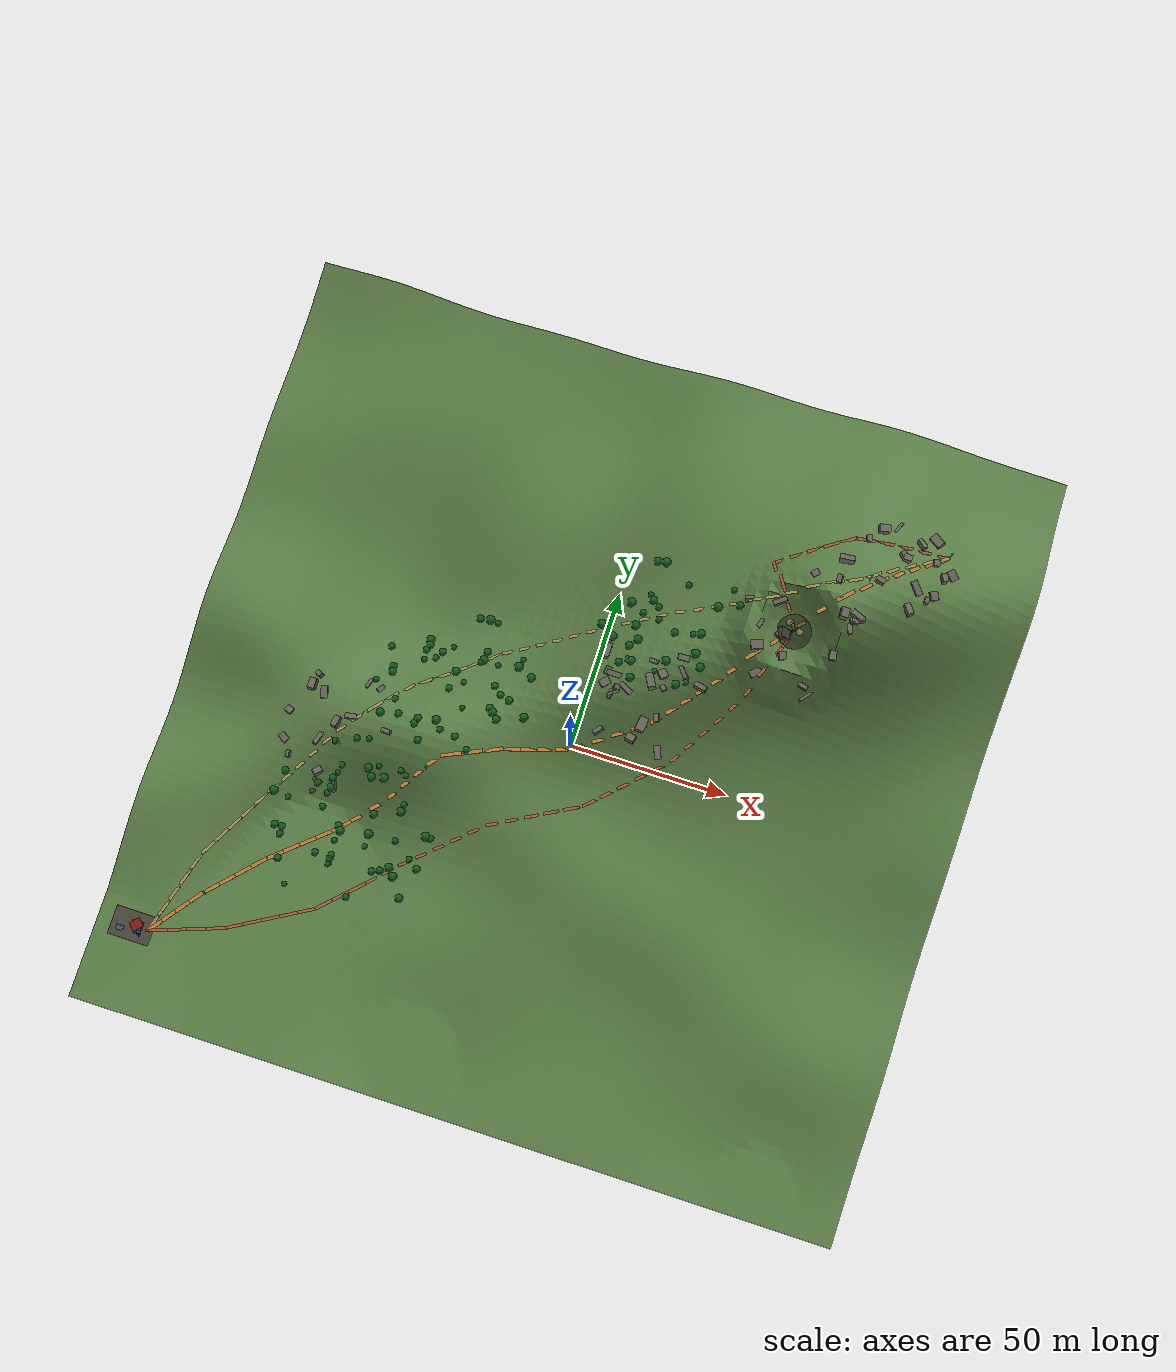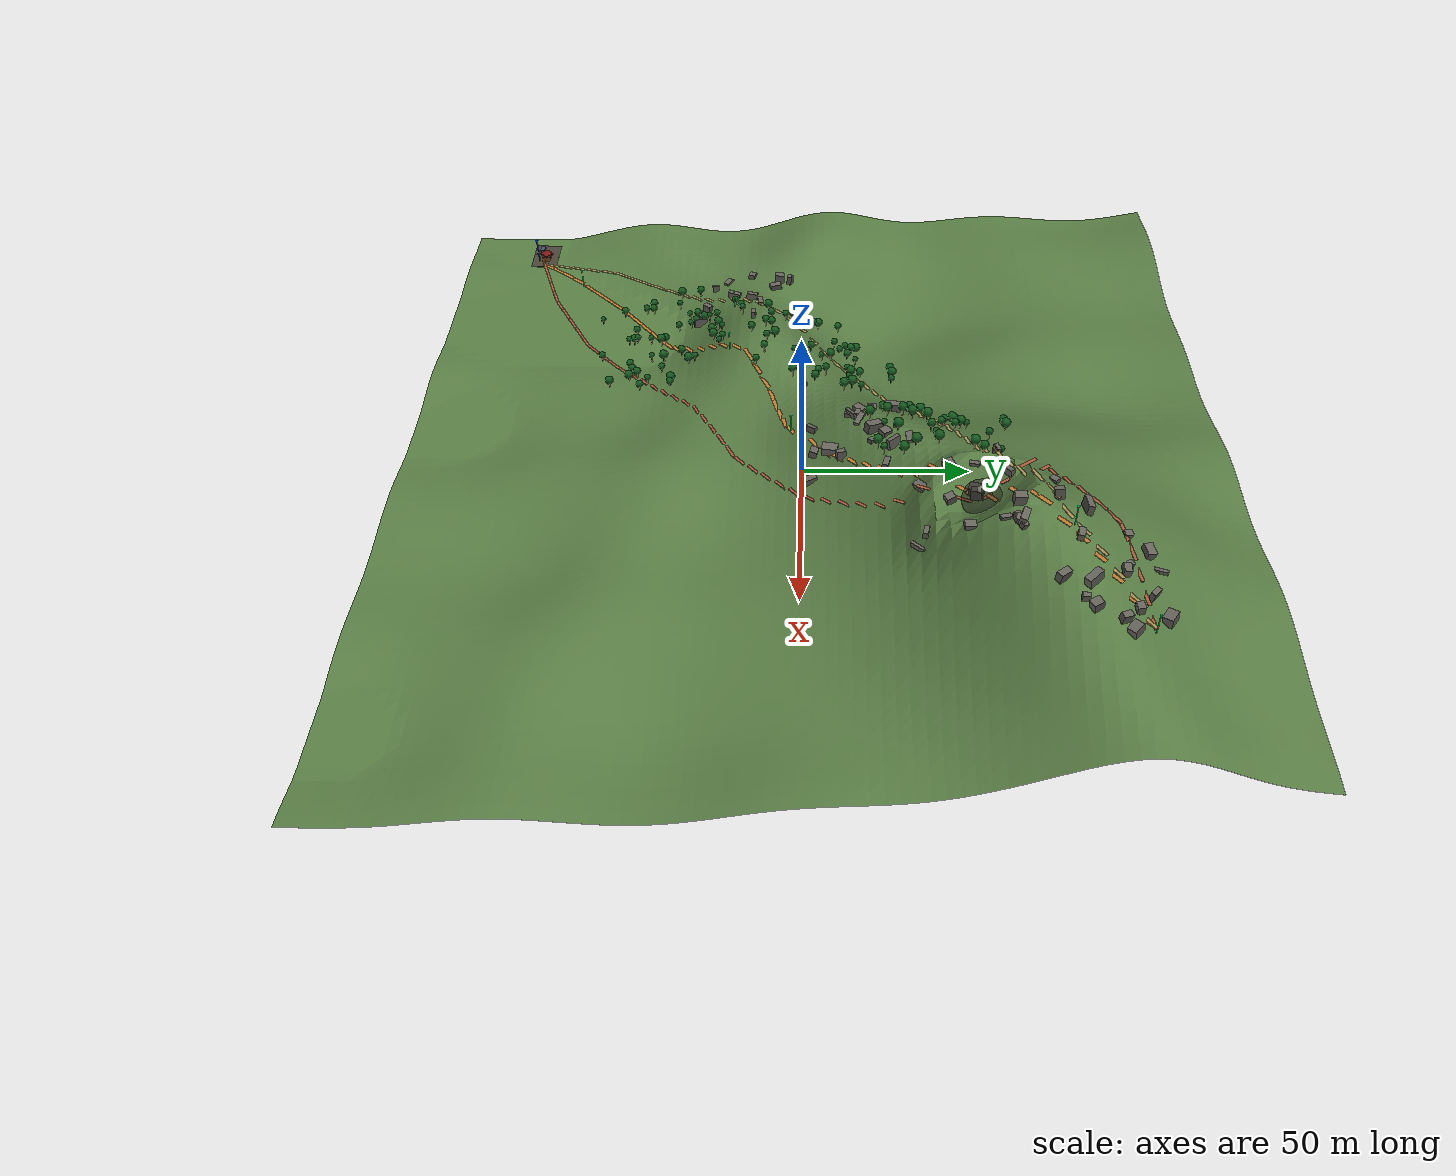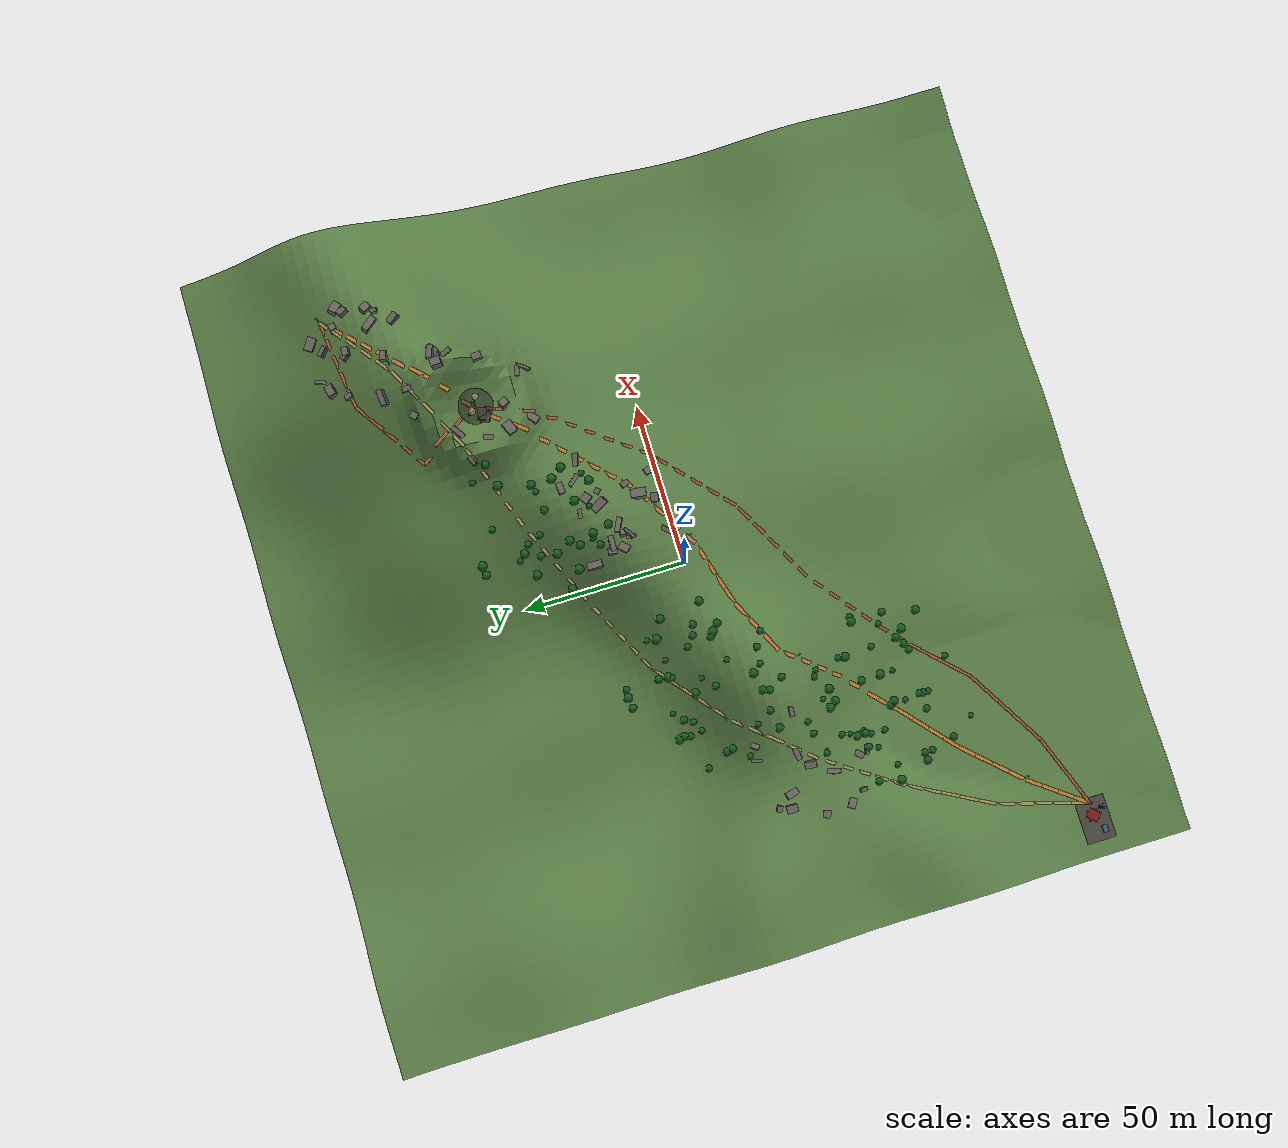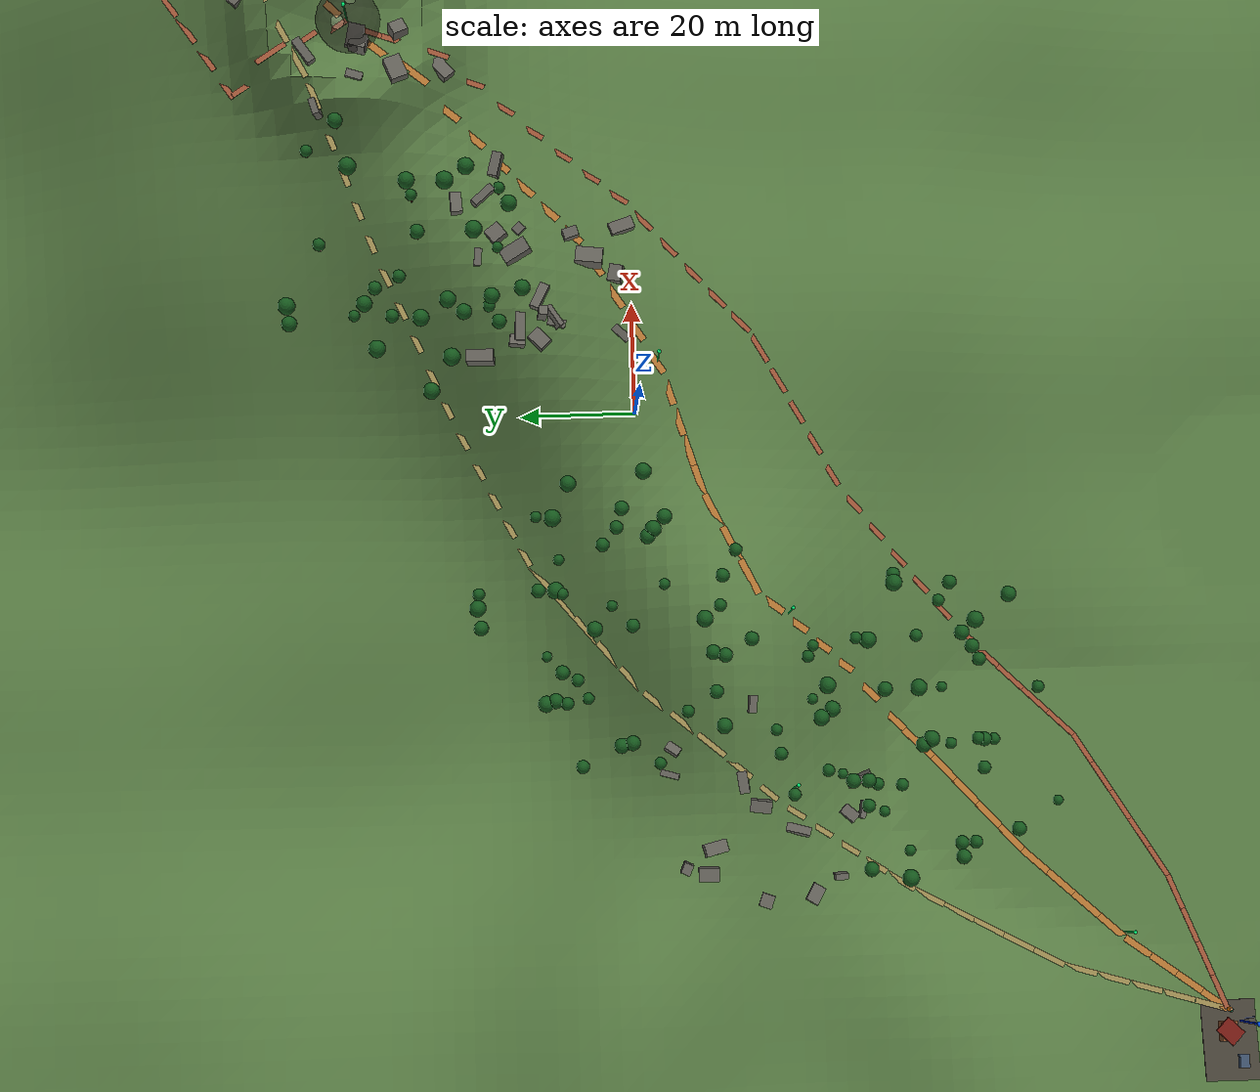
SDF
<?xml version="1.0"?>
<sdf version="1.10">
  <world name="hiking_lora_world">
    <plugin filename="gz-sim-physics-system" name="gz::sim::systems::Physics"/>
    <plugin filename="gz-sim-user-commands-system" name="gz::sim::systems::UserCommands"/>
    <plugin filename="gz-sim-scene-broadcaster-system" name="gz::sim::systems::SceneBroadcaster"/>
    <gravity>0 0 -9.81</gravity>
    <magnetic_field>5.5645e-06 2.28758e-05 -4.23884e-05</magnetic_field>
    <atmosphere type="adiabatic"/>

    <gui fullscreen="0">
      <camera name="user_camera">
        <pose>-74 -168 86 0 0.52 0.43</pose>
        <view_controller>orbit</view_controller>
      </camera>
    </gui>

    <scene>
      <ambient>0.45 0.48 0.48 1</ambient>
      <background>0.55 0.70 0.86 1</background>
      <grid>false</grid>
    </scene>

    <light name="sun" type="directional">
      <pose>0 0 120 0 0 0</pose>
      <cast_shadows>true</cast_shadows>
      <intensity>1.1</intensity>
      <direction>-0.42 0.32 -0.85</direction>
      <diffuse>0.92 0.88 0.76 1</diffuse>
      <specular>0.18 0.18 0.16 1</specular>
    </light>

    <model name="wide_mountain_terrain">
      <static>true</static>
      <link name="terrain_link">
        <collision name="terrain_collision">
          <geometry>
            <mesh>
              <uri>model://hiking_lora_terrain/meshes/mountain_terrain.dae</uri>
            </mesh>
          </geometry>
        </collision>
        <visual name="terrain_visual">
          <geometry>
            <mesh>
              <uri>model://hiking_lora_terrain/meshes/mountain_terrain.dae</uri>
            </mesh>
          </geometry>
          <material>
            <ambient>0.23 0.35 0.21 1</ambient>
            <diffuse>0.34 0.48 0.26 1</diffuse>
            <specular>0.08 0.08 0.07 1</specular>
          </material>
        </visual>
      </link>
    </model>

    <model name="trail_ridge_route">
      <static>true</static>
      <link name="trail_link">
        <visual name="ridge_route_0"><pose>-102.5 -92 0.546 0 0 0.9273</pose><geometry><box><size>5 1.15 0.08</size></box></geometry><material><ambient>0.5184 0.3384 0.144 1</ambient><diffuse>0.72 0.47 0.20 1</diffuse></material></visual>
        <visual name="ridge_route_1"><pose>-99.5 -88 0.7807 0 0 0.9273</pose><geometry><box><size>5 1.15 0.08</size></box></geometry><material><ambient>0.5184 0.3384 0.144 1</ambient><diffuse>0.72 0.47 0.20 1</diffuse></material></visual>
        <visual name="ridge_route_2"><pose>-96.5 -84 0.836 0 0 0.9273</pose><geometry><box><size>5 1.15 0.08</size></box></geometry><material><ambient>0.5184 0.3384 0.144 1</ambient><diffuse>0.72 0.47 0.20 1</diffuse></material></visual>
        <visual name="ridge_route_3"><pose>-93.5 -80 0.6716 0 0 0.9273</pose><geometry><box><size>5 1.15 0.08</size></box></geometry><material><ambient>0.5184 0.3384 0.144 1</ambient><diffuse>0.72 0.47 0.20 1</diffuse></material></visual>
        <visual name="ridge_route_4"><pose>-90.125 -76 0.49 0 0 0.8176</pose><geometry><box><size>5.4829 1.15 0.08</size></box></geometry><material><ambient>0.5184 0.3384 0.144 1</ambient><diffuse>0.72 0.47 0.20 1</diffuse></material></visual>
        <visual name="ridge_route_5"><pose>-86.375 -72 0.49 0 0 0.8176</pose><geometry><box><size>5.4829 1.15 0.08</size></box></geometry><material><ambient>0.5184 0.3384 0.144 1</ambient><diffuse>0.72 0.47 0.20 1</diffuse></material></visual>
        <visual name="ridge_route_6"><pose>-82.625 -68 0.49 0 0 0.8176</pose><geometry><box><size>5.4829 1.15 0.08</size></box></geometry><material><ambient>0.5184 0.3384 0.144 1</ambient><diffuse>0.72 0.47 0.20 1</diffuse></material></visual>
        <visual name="ridge_route_7"><pose>-78.875 -64 0.49 0 0 0.8176</pose><geometry><box><size>5.4829 1.15 0.08</size></box></geometry><material><ambient>0.5184 0.3384 0.144 1</ambient><diffuse>0.72 0.47 0.20 1</diffuse></material></visual>
        <visual name="ridge_route_8"><pose>-75 -60.25 0.49 0 0 0.7188</pose><geometry><box><size>5.3151 1.15 0.08</size></box></geometry><material><ambient>0.5184 0.3384 0.144 1</ambient><diffuse>0.72 0.47 0.20 1</diffuse></material></visual>
        <visual name="ridge_route_9"><pose>-71 -56.75 0.49 0 0 0.7188</pose><geometry><box><size>5.3151 1.15 0.08</size></box></geometry><material><ambient>0.5184 0.3384 0.144 1</ambient><diffuse>0.72 0.47 0.20 1</diffuse></material></visual>
        <visual name="ridge_route_10"><pose>-67 -53.25 0.49 0 0 0.7188</pose><geometry><box><size>5.3151 1.15 0.08</size></box></geometry><material><ambient>0.5184 0.3384 0.144 1</ambient><diffuse>0.72 0.47 0.20 1</diffuse></material></visual>
        <visual name="ridge_route_11"><pose>-63 -49.75 0.49 0 0 0.7188</pose><geometry><box><size>5.3151 1.15 0.08</size></box></geometry><material><ambient>0.5184 0.3384 0.144 1</ambient><diffuse>0.72 0.47 0.20 1</diffuse></material></visual>
        <visual name="ridge_route_12"><pose>-58.6667 -45.6667 0.49 0 0 0.7854</pose><geometry><box><size>6.5997 1.15 0.08</size></box></geometry><material><ambient>0.5184 0.3384 0.144 1</ambient><diffuse>0.72 0.47 0.20 1</diffuse></material></visual>
        <visual name="ridge_route_13"><pose>-54 -41 1.6083 0 0 0.7854</pose><geometry><box><size>6.5997 1.15 0.08</size></box></geometry><material><ambient>0.5184 0.3384 0.144 1</ambient><diffuse>0.72 0.47 0.20 1</diffuse></material></visual>
        <visual name="ridge_route_14"><pose>-49.3333 -36.3333 5.1993 0 0 0.7854</pose><geometry><box><size>6.5997 1.15 0.08</size></box></geometry><material><ambient>0.5184 0.3384 0.144 1</ambient><diffuse>0.72 0.47 0.20 1</diffuse></material></visual>
        <visual name="ridge_route_15"><pose>-45.5 -32 8.9429 0 0 0.9273</pose><geometry><box><size>5 1.15 0.08</size></box></geometry><material><ambient>0.5184 0.3384 0.144 1</ambient><diffuse>0.72 0.47 0.20 1</diffuse></material></visual>
        <visual name="ridge_route_16"><pose>-42.5 -28 12.3434 0 0 0.9273</pose><geometry><box><size>5 1.15 0.08</size></box></geometry><material><ambient>0.5184 0.3384 0.144 1</ambient><diffuse>0.72 0.47 0.20 1</diffuse></material></visual>
        <visual name="ridge_route_17"><pose>-39.5 -24 15.3419 0 0 0.9273</pose><geometry><box><size>5 1.15 0.08</size></box></geometry><material><ambient>0.5184 0.3384 0.144 1</ambient><diffuse>0.72 0.47 0.20 1</diffuse></material></visual>
        <visual name="ridge_route_18"><pose>-36.5 -20 17.5391 0 0 0.9273</pose><geometry><box><size>5 1.15 0.08</size></box></geometry><material><ambient>0.5184 0.3384 0.144 1</ambient><diffuse>0.72 0.47 0.20 1</diffuse></material></visual>
        <visual name="ridge_route_19"><pose>-32.1667 -16.6667 18.3058 0 0 0.4398</pose><geometry><box><size>6.2628 1.15 0.08</size></box></geometry><material><ambient>0.5184 0.3384 0.144 1</ambient><diffuse>0.72 0.47 0.20 1</diffuse></material></visual>
        <visual name="ridge_route_20"><pose>-26.5 -14 17.8097 0 0 0.4398</pose><geometry><box><size>6.2628 1.15 0.08</size></box></geometry><material><ambient>0.5184 0.3384 0.144 1</ambient><diffuse>0.72 0.47 0.20 1</diffuse></material></visual>
        <visual name="ridge_route_21"><pose>-20.8333 -11.3333 17.0735 0 0 0.4398</pose><geometry><box><size>6.2628 1.15 0.08</size></box></geometry><material><ambient>0.5184 0.3384 0.144 1</ambient><diffuse>0.72 0.47 0.20 1</diffuse></material></visual>
        <visual name="ridge_route_22"><pose>-15.5 -9.25 16.6199 0 0 0.2915</pose><geometry><box><size>5.2202 1.15 0.08</size></box></geometry><material><ambient>0.5184 0.3384 0.144 1</ambient><diffuse>0.72 0.47 0.20 1</diffuse></material></visual>
        <visual name="ridge_route_23"><pose>-10.5 -7.75 16.6231 0 0 0.2915</pose><geometry><box><size>5.2202 1.15 0.08</size></box></geometry><material><ambient>0.5184 0.3384 0.144 1</ambient><diffuse>0.72 0.47 0.20 1</diffuse></material></visual>
        <visual name="ridge_route_24"><pose>-5.5 -6.25 17.1872 0 0 0.2915</pose><geometry><box><size>5.2202 1.15 0.08</size></box></geometry><material><ambient>0.5184 0.3384 0.144 1</ambient><diffuse>0.72 0.47 0.20 1</diffuse></material></visual>
        <visual name="ridge_route_25"><pose>-0.5 -4.75 18.2039 0 0 0.2915</pose><geometry><box><size>5.2202 1.15 0.08</size></box></geometry><material><ambient>0.5184 0.3384 0.144 1</ambient><diffuse>0.72 0.47 0.20 1</diffuse></material></visual>
        <visual name="ridge_route_26"><pose>4.5 -2.375 19.9416 0 0 0.5764</pose><geometry><box><size>5.9634 1.15 0.08</size></box></geometry><material><ambient>0.5184 0.3384 0.144 1</ambient><diffuse>0.72 0.47 0.20 1</diffuse></material></visual>
        <visual name="ridge_route_27"><pose>9.5 0.875 22.2909 0 0 0.5764</pose><geometry><box><size>5.9634 1.15 0.08</size></box></geometry><material><ambient>0.5184 0.3384 0.144 1</ambient><diffuse>0.72 0.47 0.20 1</diffuse></material></visual>
        <visual name="ridge_route_28"><pose>14.5 4.125 24.4828 0 0 0.5764</pose><geometry><box><size>5.9634 1.15 0.08</size></box></geometry><material><ambient>0.5184 0.3384 0.144 1</ambient><diffuse>0.72 0.47 0.20 1</diffuse></material></visual>
        <visual name="ridge_route_29"><pose>19.5 7.375 26.2979 0 0 0.5764</pose><geometry><box><size>5.9634 1.15 0.08</size></box></geometry><material><ambient>0.5184 0.3384 0.144 1</ambient><diffuse>0.72 0.47 0.20 1</diffuse></material></visual>
        <visual name="ridge_route_30"><pose>23.7 10.9 28.0669 0 0 0.8409</pose><geometry><box><size>5.099 1.15 0.08</size></box></geometry><material><ambient>0.5184 0.3384 0.144 1</ambient><diffuse>0.72 0.47 0.20 1</diffuse></material></visual>
        <visual name="ridge_route_31"><pose>27.1 14.7 30.0291 0 0 0.8409</pose><geometry><box><size>5.099 1.15 0.08</size></box></geometry><material><ambient>0.5184 0.3384 0.144 1</ambient><diffuse>0.72 0.47 0.20 1</diffuse></material></visual>
        <visual name="ridge_route_32"><pose>30.5 18.5 31.9562 0 0 0.8409</pose><geometry><box><size>5.099 1.15 0.08</size></box></geometry><material><ambient>0.5184 0.3384 0.144 1</ambient><diffuse>0.72 0.47 0.20 1</diffuse></material></visual>
        <visual name="ridge_route_33"><pose>33.9 22.3 33.9446 0 0 0.8409</pose><geometry><box><size>5.099 1.15 0.08</size></box></geometry><material><ambient>0.5184 0.3384 0.144 1</ambient><diffuse>0.72 0.47 0.20 1</diffuse></material></visual>
        <visual name="ridge_route_34"><pose>37.3 26.1 36.0663 0 0 0.8409</pose><geometry><box><size>5.099 1.15 0.08</size></box></geometry><material><ambient>0.5184 0.3384 0.144 1</ambient><diffuse>0.72 0.47 0.20 1</diffuse></material></visual>
        <visual name="ridge_route_35"><pose>40.875 30.25 39.0799 0 0 0.8761</pose><geometry><box><size>5.8577 1.15 0.08</size></box></geometry><material><ambient>0.5184 0.3384 0.144 1</ambient><diffuse>0.72 0.47 0.20 1</diffuse></material></visual>
        <visual name="ridge_route_36"><pose>44.625 34.75 45.0126 0 0 0.8761</pose><geometry><box><size>5.8577 1.15 0.08</size></box></geometry><material><ambient>0.5184 0.3384 0.144 1</ambient><diffuse>0.72 0.47 0.20 1</diffuse></material></visual>
        <visual name="ridge_route_37"><pose>48.375 39.25 43.3006 0 0 0.8761</pose><geometry><box><size>5.8577 1.15 0.08</size></box></geometry><material><ambient>0.5184 0.3384 0.144 1</ambient><diffuse>0.72 0.47 0.20 1</diffuse></material></visual>
        <visual name="ridge_route_38"><pose>52.125 43.75 42.8799 0 0 0.8761</pose><geometry><box><size>5.8577 1.15 0.08</size></box></geometry><material><ambient>0.5184 0.3384 0.144 1</ambient><diffuse>0.72 0.47 0.20 1</diffuse></material></visual>
        <visual name="ridge_route_39"><pose>56.125 48.125 45.9232 0 0 0.7854</pose><geometry><box><size>6.0104 1.15 0.08</size></box></geometry><material><ambient>0.5184 0.3384 0.144 1</ambient><diffuse>0.72 0.47 0.20 1</diffuse></material></visual>
        <visual name="ridge_route_40"><pose>60.375 52.375 52.8643 0 0 0.7854</pose><geometry><box><size>6.0104 1.15 0.08</size></box></geometry><material><ambient>0.5184 0.3384 0.144 1</ambient><diffuse>0.72 0.47 0.20 1</diffuse></material></visual>
        <visual name="ridge_route_41"><pose>64.625 56.625 56.0258 0 0 0.7854</pose><geometry><box><size>6.0104 1.15 0.08</size></box></geometry><material><ambient>0.5184 0.3384 0.144 1</ambient><diffuse>0.72 0.47 0.20 1</diffuse></material></visual>
        <visual name="ridge_route_42"><pose>68.875 60.875 53.396 0 0 0.7854</pose><geometry><box><size>6.0104 1.15 0.08</size></box></geometry><material><ambient>0.5184 0.3384 0.144 1</ambient><diffuse>0.72 0.47 0.20 1</diffuse></material></visual>
        <visual name="ridge_route_43"><pose>73 64.8 52.1914 0 0 0.7328</pose><geometry><box><size>5.3814 1.15 0.08</size></box></geometry><material><ambient>0.5184 0.3384 0.144 1</ambient><diffuse>0.72 0.47 0.20 1</diffuse></material></visual>
        <visual name="ridge_route_44"><pose>77 68.4 50.272 0 0 0.7328</pose><geometry><box><size>5.3814 1.15 0.08</size></box></geometry><material><ambient>0.5184 0.3384 0.144 1</ambient><diffuse>0.72 0.47 0.20 1</diffuse></material></visual>
        <visual name="ridge_route_45"><pose>81 72 47.6791 0 0 0.7328</pose><geometry><box><size>5.3814 1.15 0.08</size></box></geometry><material><ambient>0.5184 0.3384 0.144 1</ambient><diffuse>0.72 0.47 0.20 1</diffuse></material></visual>
        <visual name="ridge_route_46"><pose>85 75.6 44.6577 0 0 0.7328</pose><geometry><box><size>5.3814 1.15 0.08</size></box></geometry><material><ambient>0.5184 0.3384 0.144 1</ambient><diffuse>0.72 0.47 0.20 1</diffuse></material></visual>
        <visual name="ridge_route_47"><pose>89 79.2 41.4617 0 0 0.7328</pose><geometry><box><size>5.3814 1.15 0.08</size></box></geometry><material><ambient>0.5184 0.3384 0.144 1</ambient><diffuse>0.72 0.47 0.20 1</diffuse></material></visual>
      </link>
    </model>
    <model name="trail_valley_route">
      <static>true</static>
      <link name="trail_link">
        <visual name="valley_route_0"><pose>-103.2 -91.3 0.546 0 0 1.2827</pose><geometry><box><size>5.6321 0.92 0.08</size></box></geometry><material><ambient>0.44639999999999996 0.396 0.2304 1</ambient><diffuse>0.62 0.55 0.32 1</diffuse></material></visual>
        <visual name="valley_route_1"><pose>-101.6 -85.9 0.9509 0 0 1.2827</pose><geometry><box><size>5.6321 0.92 0.08</size></box></geometry><material><ambient>0.44639999999999996 0.396 0.2304 1</ambient><diffuse>0.62 0.55 0.32 1</diffuse></material></visual>
        <visual name="valley_route_2"><pose>-100 -80.5 1.419 0 0 1.2827</pose><geometry><box><size>5.6321 0.92 0.08</size></box></geometry><material><ambient>0.44639999999999996 0.396 0.2304 1</ambient><diffuse>0.62 0.55 0.32 1</diffuse></material></visual>
        <visual name="valley_route_3"><pose>-98.4 -75.1 1.9051 0 0 1.2827</pose><geometry><box><size>5.6321 0.92 0.08</size></box></geometry><material><ambient>0.44639999999999996 0.396 0.2304 1</ambient><diffuse>0.62 0.55 0.32 1</diffuse></material></visual>
        <visual name="valley_route_4"><pose>-96.8 -69.7 2.3878 0 0 1.2827</pose><geometry><box><size>5.6321 0.92 0.08</size></box></geometry><material><ambient>0.44639999999999996 0.396 0.2304 1</ambient><diffuse>0.62 0.55 0.32 1</diffuse></material></visual>
        <visual name="valley_route_5"><pose>-94.7 -64.6 2.6821 0 0 1.0744</pose><geometry><box><size>5.4589 0.92 0.08</size></box></geometry><material><ambient>0.44639999999999996 0.396 0.2304 1</ambient><diffuse>0.62 0.55 0.32 1</diffuse></material></visual>
        <visual name="valley_route_6"><pose>-92.1 -59.8 2.7176 0 0 1.0744</pose><geometry><box><size>5.4589 0.92 0.08</size></box></geometry><material><ambient>0.44639999999999996 0.396 0.2304 1</ambient><diffuse>0.62 0.55 0.32 1</diffuse></material></visual>
        <visual name="valley_route_7"><pose>-89.5 -55 2.7303 0 0 1.0744</pose><geometry><box><size>5.4589 0.92 0.08</size></box></geometry><material><ambient>0.44639999999999996 0.396 0.2304 1</ambient><diffuse>0.62 0.55 0.32 1</diffuse></material></visual>
        <visual name="valley_route_8"><pose>-86.9 -50.2 2.8194 0 0 1.0744</pose><geometry><box><size>5.4589 0.92 0.08</size></box></geometry><material><ambient>0.44639999999999996 0.396 0.2304 1</ambient><diffuse>0.62 0.55 0.32 1</diffuse></material></visual>
        <visual name="valley_route_9"><pose>-84.3 -45.4 3.0976 0 0 1.0744</pose><geometry><box><size>5.4589 0.92 0.08</size></box></geometry><material><ambient>0.44639999999999996 0.396 0.2304 1</ambient><diffuse>0.62 0.55 0.32 1</diffuse></material></visual>
        <visual name="valley_route_10"><pose>-81.5 -40.7 3.5982 0 0 0.9929</pose><geometry><box><size>5.4918 0.92 0.08</size></box></geometry><material><ambient>0.44639999999999996 0.396 0.2304 1</ambient><diffuse>0.62 0.55 0.32 1</diffuse></material></visual>
        <visual name="valley_route_11"><pose>-78.5 -36.1 4.4941 0 0 0.9929</pose><geometry><box><size>5.4918 0.92 0.08</size></box></geometry><material><ambient>0.44639999999999996 0.396 0.2304 1</ambient><diffuse>0.62 0.55 0.32 1</diffuse></material></visual>
        <visual name="valley_route_12"><pose>-75.5 -31.5 6.0116 0 0 0.9929</pose><geometry><box><size>5.4918 0.92 0.08</size></box></geometry><material><ambient>0.44639999999999996 0.396 0.2304 1</ambient><diffuse>0.62 0.55 0.32 1</diffuse></material></visual>
        <visual name="valley_route_13"><pose>-72.5 -26.9 8.1344 0 0 0.9929</pose><geometry><box><size>5.4918 0.92 0.08</size></box></geometry><material><ambient>0.44639999999999996 0.396 0.2304 1</ambient><diffuse>0.62 0.55 0.32 1</diffuse></material></visual>
        <visual name="valley_route_14"><pose>-69.5 -22.3 10.5981 0 0 0.9929</pose><geometry><box><size>5.4918 0.92 0.08</size></box></geometry><material><ambient>0.44639999999999996 0.396 0.2304 1</ambient><diffuse>0.62 0.55 0.32 1</diffuse></material></visual>
        <visual name="valley_route_15"><pose>-66.2 -17.9 12.9056 0 0 0.8622</pose><geometry><box><size>5.5317 0.92 0.08</size></box></geometry><material><ambient>0.44639999999999996 0.396 0.2304 1</ambient><diffuse>0.62 0.55 0.32 1</diffuse></material></visual>
        <visual name="valley_route_16"><pose>-62.6 -13.7 14.597 0 0 0.8622</pose><geometry><box><size>5.5317 0.92 0.08</size></box></geometry><material><ambient>0.44639999999999996 0.396 0.2304 1</ambient><diffuse>0.62 0.55 0.32 1</diffuse></material></visual>
        <visual name="valley_route_17"><pose>-59 -9.5 15.2142 0 0 0.8622</pose><geometry><box><size>5.5317 0.92 0.08</size></box></geometry><material><ambient>0.44639999999999996 0.396 0.2304 1</ambient><diffuse>0.62 0.55 0.32 1</diffuse></material></visual>
        <visual name="valley_route_18"><pose>-55.4 -5.3 14.6238 0 0 0.8622</pose><geometry><box><size>5.5317 0.92 0.08</size></box></geometry><material><ambient>0.44639999999999996 0.396 0.2304 1</ambient><diffuse>0.62 0.55 0.32 1</diffuse></material></visual>
        <visual name="valley_route_19"><pose>-51.8 -1.1 13.0998 0 0 0.8622</pose><geometry><box><size>5.5317 0.92 0.08</size></box></geometry><material><ambient>0.44639999999999996 0.396 0.2304 1</ambient><diffuse>0.62 0.55 0.32 1</diffuse></material></visual>
        <visual name="valley_route_20"><pose>-47.8 2.8 11.51 0 0 0.6857</pose><geometry><box><size>5.6851 0.92 0.08</size></box></geometry><material><ambient>0.44639999999999996 0.396 0.2304 1</ambient><diffuse>0.62 0.55 0.32 1</diffuse></material></visual>
        <visual name="valley_route_21"><pose>-43.4 6.4 10.3608 0 0 0.6857</pose><geometry><box><size>5.6851 0.92 0.08</size></box></geometry><material><ambient>0.44639999999999996 0.396 0.2304 1</ambient><diffuse>0.62 0.55 0.32 1</diffuse></material></visual>
        <visual name="valley_route_22"><pose>-39 10 9.5891 0 0 0.6857</pose><geometry><box><size>5.6851 0.92 0.08</size></box></geometry><material><ambient>0.44639999999999996 0.396 0.2304 1</ambient><diffuse>0.62 0.55 0.32 1</diffuse></material></visual>
        <visual name="valley_route_23"><pose>-34.6 13.6 9.3023 0 0 0.6857</pose><geometry><box><size>5.6851 0.92 0.08</size></box></geometry><material><ambient>0.44639999999999996 0.396 0.2304 1</ambient><diffuse>0.62 0.55 0.32 1</diffuse></material></visual>
        <visual name="valley_route_24"><pose>-30.2 17.2 9.501 0 0 0.6857</pose><geometry><box><size>5.6851 0.92 0.08</size></box></geometry><material><ambient>0.44639999999999996 0.396 0.2304 1</ambient><diffuse>0.62 0.55 0.32 1</diffuse></material></visual>
        <visual name="valley_route_25"><pose>-25.7 20.2 10.3668 0 0 0.4809</pose><geometry><box><size>5.1884 0.92 0.08</size></box></geometry><material><ambient>0.44639999999999996 0.396 0.2304 1</ambient><diffuse>0.62 0.55 0.32 1</diffuse></material></visual>
        <visual name="valley_route_26"><pose>-21.1 22.6 11.8105 0 0 0.4809</pose><geometry><box><size>5.1884 0.92 0.08</size></box></geometry><material><ambient>0.44639999999999996 0.396 0.2304 1</ambient><diffuse>0.62 0.55 0.32 1</diffuse></material></visual>
        <visual name="valley_route_27"><pose>-16.5 25 13.6172 0 0 0.4809</pose><geometry><box><size>5.1884 0.92 0.08</size></box></geometry><material><ambient>0.44639999999999996 0.396 0.2304 1</ambient><diffuse>0.62 0.55 0.32 1</diffuse></material></visual>
        <visual name="valley_route_28"><pose>-11.9 27.4 15.7911 0 0 0.4809</pose><geometry><box><size>5.1884 0.92 0.08</size></box></geometry><material><ambient>0.44639999999999996 0.396 0.2304 1</ambient><diffuse>0.62 0.55 0.32 1</diffuse></material></visual>
        <visual name="valley_route_29"><pose>-7.3 29.8 18.2863 0 0 0.4809</pose><geometry><box><size>5.1884 0.92 0.08</size></box></geometry><material><ambient>0.44639999999999996 0.396 0.2304 1</ambient><diffuse>0.62 0.55 0.32 1</diffuse></material></visual>
        <visual name="valley_route_30"><pose>-2.6 32.1 21.1094 0 0 0.4298</pose><geometry><box><size>5.2802 0.92 0.08</size></box></geometry><material><ambient>0.44639999999999996 0.396 0.2304 1</ambient><diffuse>0.62 0.55 0.32 1</diffuse></material></visual>
        <visual name="valley_route_31"><pose>2.2 34.3 24.1301 0 0 0.4298</pose><geometry><box><size>5.2802 0.92 0.08</size></box></geometry><material><ambient>0.44639999999999996 0.396 0.2304 1</ambient><diffuse>0.62 0.55 0.32 1</diffuse></material></visual>
        <visual name="valley_route_32"><pose>7 36.5 27.0883 0 0 0.4298</pose><geometry><box><size>5.2802 0.92 0.08</size></box></geometry><material><ambient>0.44639999999999996 0.396 0.2304 1</ambient><diffuse>0.62 0.55 0.32 1</diffuse></material></visual>
        <visual name="valley_route_33"><pose>11.8 38.7 29.856 0 0 0.4298</pose><geometry><box><size>5.2802 0.92 0.08</size></box></geometry><material><ambient>0.44639999999999996 0.396 0.2304 1</ambient><diffuse>0.62 0.55 0.32 1</diffuse></material></visual>
        <visual name="valley_route_34"><pose>16.6 40.9 32.3727 0 0 0.4298</pose><geometry><box><size>5.2802 0.92 0.08</size></box></geometry><material><ambient>0.44639999999999996 0.396 0.2304 1</ambient><diffuse>0.62 0.55 0.32 1</diffuse></material></visual>
        <visual name="valley_route_35"><pose>21.4 42.9 34.7022 0 0 0.3588</pose><geometry><box><size>5.1264 0.92 0.08</size></box></geometry><material><ambient>0.44639999999999996 0.396 0.2304 1</ambient><diffuse>0.62 0.55 0.32 1</diffuse></material></visual>
        <visual name="valley_route_36"><pose>26.2 44.7 36.908 0 0 0.3588</pose><geometry><box><size>5.1264 0.92 0.08</size></box></geometry><material><ambient>0.44639999999999996 0.396 0.2304 1</ambient><diffuse>0.62 0.55 0.32 1</diffuse></material></visual>
        <visual name="valley_route_37"><pose>31 46.5 39.0719 0 0 0.3588</pose><geometry><box><size>5.1264 0.92 0.08</size></box></geometry><material><ambient>0.44639999999999996 0.396 0.2304 1</ambient><diffuse>0.62 0.55 0.32 1</diffuse></material></visual>
        <visual name="valley_route_38"><pose>35.8 48.3 42.2279 0 0 0.3588</pose><geometry><box><size>5.1264 0.92 0.08</size></box></geometry><material><ambient>0.44639999999999996 0.396 0.2304 1</ambient><diffuse>0.62 0.55 0.32 1</diffuse></material></visual>
        <visual name="valley_route_39"><pose>40.6 50.1 46.9269 0 0 0.3588</pose><geometry><box><size>5.1264 0.92 0.08</size></box></geometry><material><ambient>0.44639999999999996 0.396 0.2304 1</ambient><diffuse>0.62 0.55 0.32 1</diffuse></material></visual>
        <visual name="valley_route_40"><pose>45.5 52.3 48.2351 0 0 0.4795</pose><geometry><box><size>5.6356 0.92 0.08</size></box></geometry><material><ambient>0.44639999999999996 0.396 0.2304 1</ambient><diffuse>0.62 0.55 0.32 1</diffuse></material></visual>
        <visual name="valley_route_41"><pose>50.5 54.9 49.9104 0 0 0.4795</pose><geometry><box><size>5.6356 0.92 0.08</size></box></geometry><material><ambient>0.44639999999999996 0.396 0.2304 1</ambient><diffuse>0.62 0.55 0.32 1</diffuse></material></visual>
        <visual name="valley_route_42"><pose>55.5 57.5 53.7248 0 0 0.4795</pose><geometry><box><size>5.6356 0.92 0.08</size></box></geometry><material><ambient>0.44639999999999996 0.396 0.2304 1</ambient><diffuse>0.62 0.55 0.32 1</diffuse></material></visual>
        <visual name="valley_route_43"><pose>60.5 60.1 54.2184 0 0 0.4795</pose><geometry><box><size>5.6356 0.92 0.08</size></box></geometry><material><ambient>0.44639999999999996 0.396 0.2304 1</ambient><diffuse>0.62 0.55 0.32 1</diffuse></material></visual>
        <visual name="valley_route_44"><pose>65.5 62.7 52.7367 0 0 0.4795</pose><geometry><box><size>5.6356 0.92 0.08</size></box></geometry><material><ambient>0.44639999999999996 0.396 0.2304 1</ambient><diffuse>0.62 0.55 0.32 1</diffuse></material></visual>
        <visual name="valley_route_45"><pose>70.3 65.7 51.9927 0 0 0.6365</pose><geometry><box><size>5.7201 0.92 0.08</size></box></geometry><material><ambient>0.44639999999999996 0.396 0.2304 1</ambient><diffuse>0.62 0.55 0.32 1</diffuse></material></visual>
        <visual name="valley_route_46"><pose>74.9 69.1 50.2743 0 0 0.6365</pose><geometry><box><size>5.7201 0.92 0.08</size></box></geometry><material><ambient>0.44639999999999996 0.396 0.2304 1</ambient><diffuse>0.62 0.55 0.32 1</diffuse></material></visual>
        <visual name="valley_route_47"><pose>79.5 72.5 47.7458 0 0 0.6365</pose><geometry><box><size>5.7201 0.92 0.08</size></box></geometry><material><ambient>0.44639999999999996 0.396 0.2304 1</ambient><diffuse>0.62 0.55 0.32 1</diffuse></material></visual>
        <visual name="valley_route_48"><pose>84.1 75.9 44.7042 0 0 0.6365</pose><geometry><box><size>5.7201 0.92 0.08</size></box></geometry><material><ambient>0.44639999999999996 0.396 0.2304 1</ambient><diffuse>0.62 0.55 0.32 1</diffuse></material></visual>
        <visual name="valley_route_49"><pose>88.7 79.3 41.4693 0 0 0.6365</pose><geometry><box><size>5.7201 0.92 0.08</size></box></geometry><material><ambient>0.44639999999999996 0.396 0.2304 1</ambient><diffuse>0.62 0.55 0.32 1</diffuse></material></visual>
      </link>
    </model>
    <model name="trail_crater_route">
      <static>true</static>
      <link name="trail_link">
        <visual name="crater_route_0"><pose>-101.25 -93 0.5634 0 0 0.3488</pose><geometry><box><size>5.8523 0.88 0.08</size></box></geometry><material><ambient>0.4536 0.24480000000000002 0.15839999999999999 1</ambient><diffuse>0.63 0.34 0.22 1</diffuse></material></visual>
        <visual name="crater_route_1"><pose>-95.75 -91 0.57 0 0 0.3488</pose><geometry><box><size>5.8523 0.88 0.08</size></box></geometry><material><ambient>0.4536 0.24480000000000002 0.15839999999999999 1</ambient><diffuse>0.63 0.34 0.22 1</diffuse></material></visual>
        <visual name="crater_route_2"><pose>-90.25 -89 0.49 0 0 0.3488</pose><geometry><box><size>5.8523 0.88 0.08</size></box></geometry><material><ambient>0.4536 0.24480000000000002 0.15839999999999999 1</ambient><diffuse>0.63 0.34 0.22 1</diffuse></material></visual>
        <visual name="crater_route_3"><pose>-84.75 -87 0.49 0 0 0.3488</pose><geometry><box><size>5.8523 0.88 0.08</size></box></geometry><material><ambient>0.4536 0.24480000000000002 0.15839999999999999 1</ambient><diffuse>0.63 0.34 0.22 1</diffuse></material></visual>
        <visual name="crater_route_4"><pose>-79.6 -84.6 0.49 0 0 0.5281</pose><geometry><box><size>5.557 0.88 0.08</size></box></geometry><material><ambient>0.4536 0.24480000000000002 0.15839999999999999 1</ambient><diffuse>0.63 0.34 0.22 1</diffuse></material></visual>
        <visual name="crater_route_5"><pose>-74.8 -81.8 0.49 0 0 0.5281</pose><geometry><box><size>5.557 0.88 0.08</size></box></geometry><material><ambient>0.4536 0.24480000000000002 0.15839999999999999 1</ambient><diffuse>0.63 0.34 0.22 1</diffuse></material></visual>
        <visual name="crater_route_6"><pose>-70 -79 0.49 0 0 0.5281</pose><geometry><box><size>5.557 0.88 0.08</size></box></geometry><material><ambient>0.4536 0.24480000000000002 0.15839999999999999 1</ambient><diffuse>0.63 0.34 0.22 1</diffuse></material></visual>
        <visual name="crater_route_7"><pose>-65.2 -76.2 0.49 0 0 0.5281</pose><geometry><box><size>5.557 0.88 0.08</size></box></geometry><material><ambient>0.4536 0.24480000000000002 0.15839999999999999 1</ambient><diffuse>0.63 0.34 0.22 1</diffuse></material></visual>
        <visual name="crater_route_8"><pose>-60.4 -73.4 0.49 0 0 0.5281</pose><geometry><box><size>5.557 0.88 0.08</size></box></geometry><material><ambient>0.4536 0.24480000000000002 0.15839999999999999 1</ambient><diffuse>0.63 0.34 0.22 1</diffuse></material></visual>
        <visual name="crater_route_9"><pose>-56 -70 0.49 0 0 0.7854</pose><geometry><box><size>5.6569 0.88 0.08</size></box></geometry><material><ambient>0.4536 0.24480000000000002 0.15839999999999999 1</ambient><diffuse>0.63 0.34 0.22 1</diffuse></material></visual>
        <visual name="crater_route_10"><pose>-52 -66 0.49 0 0 0.7854</pose><geometry><box><size>5.6569 0.88 0.08</size></box></geometry><material><ambient>0.4536 0.24480000000000002 0.15839999999999999 1</ambient><diffuse>0.63 0.34 0.22 1</diffuse></material></visual>
        <visual name="crater_route_11"><pose>-48 -62 0.49 0 0 0.7854</pose><geometry><box><size>5.6569 0.88 0.08</size></box></geometry><material><ambient>0.4536 0.24480000000000002 0.15839999999999999 1</ambient><diffuse>0.63 0.34 0.22 1</diffuse></material></visual>
        <visual name="crater_route_12"><pose>-44 -58 0.8059 0 0 0.7854</pose><geometry><box><size>5.6569 0.88 0.08</size></box></geometry><material><ambient>0.4536 0.24480000000000002 0.15839999999999999 1</ambient><diffuse>0.63 0.34 0.22 1</diffuse></material></visual>
        <visual name="crater_route_13"><pose>-40 -54 1.8626 0 0 0.7854</pose><geometry><box><size>5.6569 0.88 0.08</size></box></geometry><material><ambient>0.4536 0.24480000000000002 0.15839999999999999 1</ambient><diffuse>0.63 0.34 0.22 1</diffuse></material></visual>
        <visual name="crater_route_14"><pose>-35.8 -50.1 3.0393 0 0 0.7124</pose><geometry><box><size>5.8138 0.88 0.08</size></box></geometry><material><ambient>0.4536 0.24480000000000002 0.15839999999999999 1</ambient><diffuse>0.63 0.34 0.22 1</diffuse></material></visual>
        <visual name="crater_route_15"><pose>-31.4 -46.3 4.4126 0 0 0.7124</pose><geometry><box><size>5.8138 0.88 0.08</size></box></geometry><material><ambient>0.4536 0.24480000000000002 0.15839999999999999 1</ambient><diffuse>0.63 0.34 0.22 1</diffuse></material></visual>
        <visual name="crater_route_16"><pose>-27 -42.5 6.0391 0 0 0.7124</pose><geometry><box><size>5.8138 0.88 0.08</size></box></geometry><material><ambient>0.4536 0.24480000000000002 0.15839999999999999 1</ambient><diffuse>0.63 0.34 0.22 1</diffuse></material></visual>
        <visual name="crater_route_17"><pose>-22.6 -38.7 7.8873 0 0 0.7124</pose><geometry><box><size>5.8138 0.88 0.08</size></box></geometry><material><ambient>0.4536 0.24480000000000002 0.15839999999999999 1</ambient><diffuse>0.63 0.34 0.22 1</diffuse></material></visual>
        <visual name="crater_route_18"><pose>-18.2 -34.9 9.766 0 0 0.7124</pose><geometry><box><size>5.8138 0.88 0.08</size></box></geometry><material><ambient>0.4536 0.24480000000000002 0.15839999999999999 1</ambient><diffuse>0.63 0.34 0.22 1</diffuse></material></visual>
        <visual name="crater_route_19"><pose>-13.4 -31.6 11.3059 0 0 0.4939</pose><geometry><box><size>5.9059 0.88 0.08</size></box></geometry><material><ambient>0.4536 0.24480000000000002 0.15839999999999999 1</ambient><diffuse>0.63 0.34 0.22 1</diffuse></material></visual>
        <visual name="crater_route_20"><pose>-8.2 -28.8 12.4839 0 0 0.4939</pose><geometry><box><size>5.9059 0.88 0.08</size></box></geometry><material><ambient>0.4536 0.24480000000000002 0.15839999999999999 1</ambient><diffuse>0.63 0.34 0.22 1</diffuse></material></visual>
        <visual name="crater_route_21"><pose>-3 -26 13.4171 0 0 0.4939</pose><geometry><box><size>5.9059 0.88 0.08</size></box></geometry><material><ambient>0.4536 0.24480000000000002 0.15839999999999999 1</ambient><diffuse>0.63 0.34 0.22 1</diffuse></material></visual>
        <visual name="crater_route_22"><pose>2.2 -23.2 14.1332 0 0 0.4939</pose><geometry><box><size>5.9059 0.88 0.08</size></box></geometry><material><ambient>0.4536 0.24480000000000002 0.15839999999999999 1</ambient><diffuse>0.63 0.34 0.22 1</diffuse></material></visual>
        <visual name="crater_route_23"><pose>7.4 -20.4 14.6916 0 0 0.4939</pose><geometry><box><size>5.9059 0.88 0.08</size></box></geometry><material><ambient>0.4536 0.24480000000000002 0.15839999999999999 1</ambient><diffuse>0.63 0.34 0.22 1</diffuse></material></visual>
        <visual name="crater_route_24"><pose>12.1 -17 15.2202 0 0 0.761</pose><geometry><box><size>5.8 0.88 0.08</size></box></geometry><material><ambient>0.4536 0.24480000000000002 0.15839999999999999 1</ambient><diffuse>0.63 0.34 0.22 1</diffuse></material></visual>
        <visual name="crater_route_25"><pose>16.3 -13 16.0091 0 0 0.761</pose><geometry><box><size>5.8 0.88 0.08</size></box></geometry><material><ambient>0.4536 0.24480000000000002 0.15839999999999999 1</ambient><diffuse>0.63 0.34 0.22 1</diffuse></material></visual>
        <visual name="crater_route_26"><pose>20.5 -9 17.0763 0 0 0.761</pose><geometry><box><size>5.8 0.88 0.08</size></box></geometry><material><ambient>0.4536 0.24480000000000002 0.15839999999999999 1</ambient><diffuse>0.63 0.34 0.22 1</diffuse></material></visual>
        <visual name="crater_route_27"><pose>24.7 -5 18.3252 0 0 0.761</pose><geometry><box><size>5.8 0.88 0.08</size></box></geometry><material><ambient>0.4536 0.24480000000000002 0.15839999999999999 1</ambient><diffuse>0.63 0.34 0.22 1</diffuse></material></visual>
        <visual name="crater_route_28"><pose>28.9 -1 19.6502 0 0 0.761</pose><geometry><box><size>5.8 0.88 0.08</size></box></geometry><material><ambient>0.4536 0.24480000000000002 0.15839999999999999 1</ambient><diffuse>0.63 0.34 0.22 1</diffuse></material></visual>
        <visual name="crater_route_29"><pose>32.5 3.3 21.2844 0 0 0.9929</pose><geometry><box><size>5.4918 0.88 0.08</size></box></geometry><material><ambient>0.4536 0.24480000000000002 0.15839999999999999 1</ambient><diffuse>0.63 0.34 0.22 1</diffuse></material></visual>
        <visual name="crater_route_30"><pose>35.5 7.9 23.3417 0 0 0.9929</pose><geometry><box><size>5.4918 0.88 0.08</size></box></geometry><material><ambient>0.4536 0.24480000000000002 0.15839999999999999 1</ambient><diffuse>0.63 0.34 0.22 1</diffuse></material></visual>
        <visual name="crater_route_31"><pose>38.5 12.5 25.6463 0 0 0.9929</pose><geometry><box><size>5.4918 0.88 0.08</size></box></geometry><material><ambient>0.4536 0.24480000000000002 0.15839999999999999 1</ambient><diffuse>0.63 0.34 0.22 1</diffuse></material></visual>
        <visual name="crater_route_32"><pose>41.5 17.1 28.2844 0 0 0.9929</pose><geometry><box><size>5.4918 0.88 0.08</size></box></geometry><material><ambient>0.4536 0.24480000000000002 0.15839999999999999 1</ambient><diffuse>0.63 0.34 0.22 1</diffuse></material></visual>
        <visual name="crater_route_33"><pose>44.5 21.7 31.2999 0 0 0.9929</pose><geometry><box><size>5.4918 0.88 0.08</size></box></geometry><material><ambient>0.4536 0.24480000000000002 0.15839999999999999 1</ambient><diffuse>0.63 0.34 0.22 1</diffuse></material></visual>
        <visual name="crater_route_34"><pose>47 26.625 35.542 0 0 1.2068</pose><geometry><box><size>5.6181 0.88 0.08</size></box></geometry><material><ambient>0.4536 0.24480000000000002 0.15839999999999999 1</ambient><diffuse>0.63 0.34 0.22 1</diffuse></material></visual>
        <visual name="crater_route_35"><pose>49 31.875 42.7591 0 0 1.2068</pose><geometry><box><size>5.6181 0.88 0.08</size></box></geometry><material><ambient>0.4536 0.24480000000000002 0.15839999999999999 1</ambient><diffuse>0.63 0.34 0.22 1</diffuse></material></visual>
        <visual name="crater_route_36"><pose>51 37.125 42.5673 0 0 1.2068</pose><geometry><box><size>5.6181 0.88 0.08</size></box></geometry><material><ambient>0.4536 0.24480000000000002 0.15839999999999999 1</ambient><diffuse>0.63 0.34 0.22 1</diffuse></material></visual>
        <visual name="crater_route_37"><pose>53 42.375 42.4839 0 0 1.2068</pose><geometry><box><size>5.6181 0.88 0.08</size></box></geometry><material><ambient>0.4536 0.24480000000000002 0.15839999999999999 1</ambient><diffuse>0.63 0.34 0.22 1</diffuse></material></visual>
        <visual name="crater_route_38"><pose>52.5 47.25 44.3152 0 0 2.1588</pose><geometry><box><size>5.4083 0.88 0.08</size></box></geometry><material><ambient>0.4536 0.24480000000000002 0.15839999999999999 1</ambient><diffuse>0.63 0.34 0.22 1</diffuse></material></visual>
        <visual name="crater_route_39"><pose>49.5 51.75 46.8837 0 0 2.1588</pose><geometry><box><size>5.4083 0.88 0.08</size></box></geometry><material><ambient>0.4536 0.24480000000000002 0.15839999999999999 1</ambient><diffuse>0.63 0.34 0.22 1</diffuse></material></visual>
        <visual name="crater_route_40"><pose>46.5 56.25 49.4617 0 0 2.1588</pose><geometry><box><size>5.4083 0.88 0.08</size></box></geometry><material><ambient>0.4536 0.24480000000000002 0.15839999999999999 1</ambient><diffuse>0.63 0.34 0.22 1</diffuse></material></visual>
        <visual name="crater_route_41"><pose>43.5 60.75 44.2823 0 0 2.1588</pose><geometry><box><size>5.4083 0.88 0.08</size></box></geometry><material><ambient>0.4536 0.24480000000000002 0.15839999999999999 1</ambient><diffuse>0.63 0.34 0.22 1</diffuse></material></visual>
        <visual name="crater_route_42"><pose>44.1 64.4 43.2066 0 0 0.588</pose><geometry><box><size>5.0478 0.88 0.08</size></box></geometry><material><ambient>0.4536 0.24480000000000002 0.15839999999999999 1</ambient><diffuse>0.63 0.34 0.22 1</diffuse></material></visual>
        <visual name="crater_route_43"><pose>48.3 67.2 44.5323 0 0 0.588</pose><geometry><box><size>5.0478 0.88 0.08</size></box></geometry><material><ambient>0.4536 0.24480000000000002 0.15839999999999999 1</ambient><diffuse>0.63 0.34 0.22 1</diffuse></material></visual>
        <visual name="crater_route_44"><pose>52.5 70 45.5287 0 0 0.588</pose><geometry><box><size>5.0478 0.88 0.08</size></box></geometry><material><ambient>0.4536 0.24480000000000002 0.15839999999999999 1</ambient><diffuse>0.63 0.34 0.22 1</diffuse></material></visual>
        <visual name="crater_route_45"><pose>56.7 72.8 46.0387 0 0 0.588</pose><geometry><box><size>5.0478 0.88 0.08</size></box></geometry><material><ambient>0.4536 0.24480000000000002 0.15839999999999999 1</ambient><diffuse>0.63 0.34 0.22 1</diffuse></material></visual>
        <visual name="crater_route_46"><pose>60.9 75.6 45.9165 0 0 0.588</pose><geometry><box><size>5.0478 0.88 0.08</size></box></geometry><material><ambient>0.4536 0.24480000000000002 0.15839999999999999 1</ambient><diffuse>0.63 0.34 0.22 1</diffuse></material></visual>
        <visual name="crater_route_47"><pose>65.8 77.4 45.7266 0 0 0.1419</pose><geometry><box><size>5.6569 0.88 0.08</size></box></geometry><material><ambient>0.4536 0.24480000000000002 0.15839999999999999 1</ambient><diffuse>0.63 0.34 0.22 1</diffuse></material></visual>
        <visual name="crater_route_48"><pose>71.4 78.2 45.3522 0 0 0.1419</pose><geometry><box><size>5.6569 0.88 0.08</size></box></geometry><material><ambient>0.4536 0.24480000000000002 0.15839999999999999 1</ambient><diffuse>0.63 0.34 0.22 1</diffuse></material></visual>
        <visual name="crater_route_49"><pose>77 79 44.222 0 0 0.1419</pose><geometry><box><size>5.6569 0.88 0.08</size></box></geometry><material><ambient>0.4536 0.24480000000000002 0.15839999999999999 1</ambient><diffuse>0.63 0.34 0.22 1</diffuse></material></visual>
        <visual name="crater_route_50"><pose>82.6 79.8 42.5789 0 0 0.1419</pose><geometry><box><size>5.6569 0.88 0.08</size></box></geometry><material><ambient>0.4536 0.24480000000000002 0.15839999999999999 1</ambient><diffuse>0.63 0.34 0.22 1</diffuse></material></visual>
        <visual name="crater_route_51"><pose>88.2 80.6 40.7536 0 0 0.1419</pose><geometry><box><size>5.6569 0.88 0.08</size></box></geometry><material><ambient>0.4536 0.24480000000000002 0.15839999999999999 1</ambient><diffuse>0.63 0.34 0.22 1</diffuse></material></visual>
      </link>
    </model>

    <model name="base_camp">
      <static>true</static>
      <pose>-109 -94 0 0 0 0</pose>
      <link name="camp_link">
        <visual name="platform"><pose>0 0 0.43 0 0 0</pose><geometry><box><size>13 9 0.16</size></box></geometry><material><ambient>0.2016 0.1872 0.15839999999999999 1</ambient><diffuse>0.28 0.26 0.22 1</diffuse></material></visual>
        <visual name="hut"><pose>1.5 0.5 1.35 0 0 0</pose><geometry><box><size>3.2 2.6 2.0</size></box></geometry><material><ambient>0.38880000000000003 0.2304 0.12240000000000001 1</ambient><diffuse>0.54 0.32 0.17 1</diffuse></material></visual>
        <visual name="roof"><pose>1.5 0.5 2.55 0 0 0.785</pose><geometry><box><size>3.5 3.0 0.45</size></box></geometry><material><ambient>0.3312 0.072 0.0504 1</ambient><diffuse>0.46 0.10 0.07 1</diffuse></material></visual>
        <visual name="equipment"><pose>-3.4 -1.8 0.9 0 0 0</pose><geometry><box><size>2.2 1.5 1.1</size></box></geometry><material><ambient>0.17279999999999998 0.2304 0.3024 1</ambient><diffuse>0.24 0.32 0.42 1</diffuse></material></visual>
      </link>
    </model>

    <model name="base_station">
      <static>true</static>
      <pose>-106 -96 0 0 0 0</pose>
      <link name="tower">
        <visual name="mast"><pose>0 0 4.6 0 0 0</pose><geometry><cylinder><radius>0.17</radius><length>8.5</length></cylinder></geometry><material><ambient>0.0 0.1296 0.648 1</ambient><diffuse>0.0 0.18 0.9 1</diffuse></material></visual>
        <visual name="antenna"><pose>0 0 9.2 0 0 0</pose><geometry><sphere><radius>0.42</radius></sphere></geometry><material><ambient>0.0 0.252 0.72 1</ambient><diffuse>0.0 0.35 1.0 1</diffuse></material></visual>
        <visual name="radio_panel"><pose>0.75 -0.2 4.35 0 0.25 0</pose><geometry><box><size>0.12 1.4 1.0</size></box></geometry><material><ambient>0.021599999999999998 0.043199999999999995 0.1152 1</ambient><diffuse>0.03 0.06 0.16 1</diffuse></material></visual>
      </link>
    </model>
    <model name="node_basecamp_gate">
      <static>true</static>
      <pose>-91 -78 0 0 0 0</pose>
      <link name="tower">
        <visual name="mast"><pose>0 0 3.35 0 0 0</pose><geometry><cylinder><radius>0.12</radius><length>6</length></cylinder></geometry><material><ambient>0.0 0.6624 0.2592 1</ambient><diffuse>0.0 0.92 0.36 1</diffuse></material></visual>
        <visual name="antenna"><pose>0 0 6.7 0 0 0</pose><geometry><sphere><radius>0.31</radius></sphere></geometry><material><ambient>0.0 0.72 0.34559999999999996 1</ambient><diffuse>0.0 1.0 0.48 1</diffuse></material></visual>
      </link>
    </model>
    <model name="node_valley_watch">
      <static>true</static>
      <pose>-66 -23 0 0 0 0</pose>
      <link name="tower">
        <visual name="mast"><pose>0 0 13.8686 0 0 0</pose><geometry><cylinder><radius>0.12</radius><length>6</length></cylinder></geometry><material><ambient>0.0 0.6624 0.2592 1</ambient><diffuse>0.0 0.92 0.36 1</diffuse></material></visual>
        <visual name="antenna"><pose>0 0 17.2186 0 0 0</pose><geometry><sphere><radius>0.31</radius></sphere></geometry><material><ambient>0.0 0.72 0.34559999999999996 1</ambient><diffuse>0.0 1.0 0.48 1</diffuse></material></visual>
      </link>
    </model>
    <model name="node_forest_pass">
      <static>true</static>
      <pose>-38 -23 0 0 0 0</pose>
      <link name="tower">
        <visual name="mast"><pose>0 0 18.8237 0 0 0</pose><geometry><cylinder><radius>0.12</radius><length>6</length></cylinder></geometry><material><ambient>0.0 0.6624 0.2592 1</ambient><diffuse>0.0 0.92 0.36 1</diffuse></material></visual>
        <visual name="antenna"><pose>0 0 22.1737 0 0 0</pose><geometry><sphere><radius>0.31</radius></sphere></geometry><material><ambient>0.0 0.72 0.34559999999999996 1</ambient><diffuse>0.0 1.0 0.48 1</diffuse></material></visual>
      </link>
    </model>
    <model name="node_ridge_mid">
      <static>true</static>
      <pose>4 -3 0 0 0 0</pose>
      <link name="tower">
        <visual name="mast"><pose>0 0 22.4037 0 0 0</pose><geometry><cylinder><radius>0.12</radius><length>6</length></cylinder></geometry><material><ambient>0.0 0.6624 0.2592 1</ambient><diffuse>0.0 0.92 0.36 1</diffuse></material></visual>
        <visual name="antenna"><pose>0 0 25.7537 0 0 0</pose><geometry><sphere><radius>0.31</radius></sphere></geometry><material><ambient>0.0 0.72 0.34559999999999996 1</ambient><diffuse>0.0 1.0 0.48 1</diffuse></material></visual>
      </link>
    </model>
    <model name="node_crater_edge">
      <static>true</static>
      <pose>54 45 0 0 0 0</pose>
      <link name="tower">
        <visual name="mast"><pose>0 0 46.4676 0 0 0</pose><geometry><cylinder><radius>0.12</radius><length>6</length></cylinder></geometry><material><ambient>0.0 0.6624 0.2592 1</ambient><diffuse>0.0 0.92 0.36 1</diffuse></material></visual>
        <visual name="antenna"><pose>0 0 49.8176 0 0 0</pose><geometry><sphere><radius>0.31</radius></sphere></geometry><material><ambient>0.0 0.72 0.34559999999999996 1</ambient><diffuse>0.0 1.0 0.48 1</diffuse></material></visual>
      </link>
    </model>
    <model name="node_north_saddle">
      <static>true</static>
      <pose>70 64 0 0 0 0</pose>
      <link name="tower">
        <visual name="mast"><pose>0 0 55.4339 0 0 0</pose><geometry><cylinder><radius>0.12</radius><length>6</length></cylinder></geometry><material><ambient>0.0 0.6624 0.2592 1</ambient><diffuse>0.0 0.92 0.36 1</diffuse></material></visual>
        <visual name="antenna"><pose>0 0 58.7839 0 0 0</pose><geometry><sphere><radius>0.31</radius></sphere></geometry><material><ambient>0.0 0.72 0.34559999999999996 1</ambient><diffuse>0.0 1.0 0.48 1</diffuse></material></visual>
      </link>
    </model>
    <model name="node_summit_view">
      <static>true</static>
      <pose>91 81 0 0 0 0</pose>
      <link name="tower">
        <visual name="mast"><pose>0 0 42.7321 0 0 0</pose><geometry><cylinder><radius>0.12</radius><length>6</length></cylinder></geometry><material><ambient>0.0 0.6624 0.2592 1</ambient><diffuse>0.0 0.92 0.36 1</diffuse></material></visual>
        <visual name="antenna"><pose>0 0 46.0821 0 0 0</pose><geometry><sphere><radius>0.31</radius></sphere></geometry><material><ambient>0.0 0.72 0.34559999999999996 1</ambient><diffuse>0.0 1.0 0.48 1</diffuse></material></visual>
      </link>
    </model>

    <model name="lower_dense_forest_trees">
      <static>true</static>
      <link name="trees">
        <visual name="trunk_0"><pose>-76.614 -42.5169 2.585 0 0 0</pose><geometry><cylinder><radius>0.1109</radius><length>2.4331</length></cylinder></geometry><material><ambient>0.2016 0.12240000000000001 0.0576 1</ambient><diffuse>0.28 0.17 0.08 1</diffuse></material></visual>
        <visual name="canopy_0"><pose>-76.614 -42.5169 4.3161 0 0 0</pose><geometry><sphere><radius>0.9356</radius></sphere></geometry><material><ambient>0.0576 0.24480000000000002 0.07919999999999999 1</ambient><diffuse>0.08 0.34 0.11 1</diffuse></material></visual>
        <visual name="trunk_1"><pose>-64.9791 -35.9901 4.2843 0 0 0</pose><geometry><cylinder><radius>0.1581</radius><length>2.5914</length></cylinder></geometry><material><ambient>0.2016 0.12240000000000001 0.0576 1</ambient><diffuse>0.28 0.17 0.08 1</diffuse></material></visual>
        <visual name="canopy_1"><pose>-64.9791 -35.9901 6.2754 0 0 0</pose><geometry><sphere><radius>1.2644</radius></sphere></geometry><material><ambient>0.0576 0.24480000000000002 0.07919999999999999 1</ambient><diffuse>0.08 0.34 0.11 1</diffuse></material></visual>
        <visual name="trunk_2"><pose>-75.5056 -53.8502 1.2799 0 0 0</pose><geometry><cylinder><radius>0.123</radius><length>1.8598</length></cylinder></geometry><material><ambient>0.2016 0.12240000000000001 0.0576 1</ambient><diffuse>0.28 0.17 0.08 1</diffuse></material></visual>
        <visual name="canopy_2"><pose>-75.5056 -53.8502 2.8226 0 0 0</pose><geometry><sphere><radius>1.114</radius></sphere></geometry><material><ambient>0.0576 0.24480000000000002 0.07919999999999999 1</ambient><diffuse>0.08 0.34 0.11 1</diffuse></material></visual>
        <visual name="trunk_3"><pose>-49.5615 -49.6476 1.6504 0 0 0</pose><geometry><cylinder><radius>0.165</radius><length>2.6007</length></cylinder></geometry><material><ambient>0.2016 0.12240000000000001 0.0576 1</ambient><diffuse>0.28 0.17 0.08 1</diffuse></material></visual>
        <visual name="canopy_3"><pose>-49.5615 -49.6476 3.4428 0 0 0</pose><geometry><sphere><radius>0.8948</radius></sphere></geometry><material><ambient>0.0576 0.24480000000000002 0.07919999999999999 1</ambient><diffuse>0.08 0.34 0.11 1</diffuse></material></visual>
        <visual name="trunk_4"><pose>-63.9276 -31.3282 7.3882 0 0 0</pose><geometry><cylinder><radius>0.1149</radius><length>2.6266</length></cylinder></geometry><material><ambient>0.2016 0.12240000000000001 0.0576 1</ambient><diffuse>0.28 0.17 0.08 1</diffuse></material></visual>
        <visual name="canopy_4"><pose>-63.9276 -31.3282 9.1751 0 0 0</pose><geometry><sphere><radius>0.8612</radius></sphere></geometry><material><ambient>0.0576 0.24480000000000002 0.07919999999999999 1</ambient><diffuse>0.08 0.34 0.11 1</diffuse></material></visual>
        <visual name="trunk_5"><pose>-38.4187 -55.8014 2.8603 0 0 0</pose><geometry><cylinder><radius>0.1857</radius><length>1.8001</length></cylinder></geometry><material><ambient>0.2016 0.12240000000000001 0.0576 1</ambient><diffuse>0.28 0.17 0.08 1</diffuse></material></visual>
        <visual name="canopy_5"><pose>-38.4187 -55.8014 4.5536 0 0 0</pose><geometry><sphere><radius>1.4423</radius></sphere></geometry><material><ambient>0.0576 0.24480000000000002 0.07919999999999999 1</ambient><diffuse>0.08 0.34 0.11 1</diffuse></material></visual>
        <visual name="trunk_6"><pose>-41.6457 -34.5903 8.6055 0 0 0</pose><geometry><cylinder><radius>0.1597</radius><length>1.8486</length></cylinder></geometry><material><ambient>0.2016 0.12240000000000001 0.0576 1</ambient><diffuse>0.28 0.17 0.08 1</diffuse></material></visual>
        <visual name="canopy_6"><pose>-41.6457 -34.5903 10.1004 0 0 0</pose><geometry><sphere><radius>1.0375</radius></sphere></geometry><material><ambient>0.0576 0.24480000000000002 0.07919999999999999 1</ambient><diffuse>0.08 0.34 0.11 1</diffuse></material></visual>
        <visual name="trunk_7"><pose>-43.3475 -26.7072 13.9483 0 0 0</pose><geometry><cylinder><radius>0.1753</radius><length>1.7565</length></cylinder></geometry><material><ambient>0.2016 0.12240000000000001 0.0576 1</ambient><diffuse>0.28 0.17 0.08 1</diffuse></material></visual>
        <visual name="canopy_7"><pose>-43.3475 -26.7072 15.3506 0 0 0</pose><geometry><sphere><radius>0.9527</radius></sphere></geometry><material><ambient>0.0576 0.24480000000000002 0.07919999999999999 1</ambient><diffuse>0.08 0.34 0.11 1</diffuse></material></visual>
        <visual name="trunk_8"><pose>-69.17 -35.7753 4.3756 0 0 0</pose><geometry><cylinder><radius>0.1408</radius><length>2.3556</length></cylinder></geometry><material><ambient>0.2016 0.12240000000000001 0.0576 1</ambient><diffuse>0.28 0.17 0.08 1</diffuse></material></visual>
        <visual name="canopy_8"><pose>-69.17 -35.7753 6.1782 0 0 0</pose><geometry><sphere><radius>1.1361</radius></sphere></geometry><material><ambient>0.0576 0.24480000000000002 0.07919999999999999 1</ambient><diffuse>0.08 0.34 0.11 1</diffuse></material></visual>
        <visual name="trunk_9"><pose>-32.4104 -41.618 6.9314 0 0 0</pose><geometry><cylinder><radius>0.1631</radius><length>2.7642</length></cylinder></geometry><material><ambient>0.2016 0.12240000000000001 0.0576 1</ambient><diffuse>0.28 0.17 0.08 1</diffuse></material></visual>
        <visual name="canopy_9"><pose>-32.4104 -41.618 9.1032 0 0 0</pose><geometry><sphere><radius>1.4358</radius></sphere></geometry><material><ambient>0.0576 0.24480000000000002 0.07919999999999999 1</ambient><diffuse>0.08 0.34 0.11 1</diffuse></material></visual>
        <visual name="trunk_10"><pose>-65.0804 -33.2287 5.954 0 0 0</pose><geometry><cylinder><radius>0.1191</radius><length>2.4591</length></cylinder></geometry><material><ambient>0.2016 0.12240000000000001 0.0576 1</ambient><diffuse>0.28 0.17 0.08 1</diffuse></material></visual>
        <visual name="canopy_10"><pose>-65.0804 -33.2287 7.8734 0 0 0</pose><geometry><sphere><radius>1.2543</radius></sphere></geometry><material><ambient>0.0576 0.24480000000000002 0.07919999999999999 1</ambient><diffuse>0.08 0.34 0.11 1</diffuse></material></visual>
        <visual name="trunk_11"><pose>-53.4656 -29.7979 10.0758 0 0 0</pose><geometry><cylinder><radius>0.15</radius><length>2.2625</length></cylinder></geometry><material><ambient>0.2016 0.12240000000000001 0.0576 1</ambient><diffuse>0.28 0.17 0.08 1</diffuse></material></visual>
        <visual name="canopy_11"><pose>-53.4656 -29.7979 11.9419 0 0 0</pose><geometry><sphere><radius>1.3361</radius></sphere></geometry><material><ambient>0.0576 0.24480000000000002 0.07919999999999999 1</ambient><diffuse>0.08 0.34 0.11 1</diffuse></material></visual>
        <visual name="trunk_12"><pose>-30.8941 -41.6924 6.8024 0 0 0</pose><geometry><cylinder><radius>0.1278</radius><length>2.1732</length></cylinder></geometry><material><ambient>0.2016 0.12240000000000001 0.0576 1</ambient><diffuse>0.28 0.17 0.08 1</diffuse></material></visual>
        <visual name="canopy_12"><pose>-30.8941 -41.6924 8.5277 0 0 0</pose><geometry><sphere><radius>1.1614</radius></sphere></geometry><material><ambient>0.0576 0.24480000000000002 0.07919999999999999 1</ambient><diffuse>0.08 0.34 0.11 1</diffuse></material></visual>
        <visual name="trunk_13"><pose>-70.096 -38.5743 3.0629 0 0 0</pose><geometry><cylinder><radius>0.154</radius><length>2.5491</length></cylinder></geometry><material><ambient>0.2016 0.12240000000000001 0.0576 1</ambient><diffuse>0.28 0.17 0.08 1</diffuse></material></visual>
        <visual name="canopy_13"><pose>-70.096 -38.5743 4.8388 0 0 0</pose><geometry><sphere><radius>0.9116</radius></sphere></geometry><material><ambient>0.0576 0.24480000000000002 0.07919999999999999 1</ambient><diffuse>0.08 0.34 0.11 1</diffuse></material></visual>
        <visual name="trunk_14"><pose>-45.1609 -25.7392 14.4449 0 0 0</pose><geometry><cylinder><radius>0.1375</radius><length>1.7405</length></cylinder></geometry><material><ambient>0.2016 0.12240000000000001 0.0576 1</ambient><diffuse>0.28 0.17 0.08 1</diffuse></material></visual>
        <visual name="canopy_14"><pose>-45.1609 -25.7392 15.874 0 0 0</pose><geometry><sphere><radius>1.0159</radius></sphere></geometry><material><ambient>0.0576 0.24480000000000002 0.07919999999999999 1</ambient><diffuse>0.08 0.34 0.11 1</diffuse></material></visual>
        <visual name="trunk_15"><pose>-59.0176 -50.6701 1.4526 0 0 0</pose><geometry><cylinder><radius>0.1326</radius><length>2.2052</length></cylinder></geometry><material><ambient>0.2016 0.12240000000000001 0.0576 1</ambient><diffuse>0.28 0.17 0.08 1</diffuse></material></visual>
        <visual name="canopy_15"><pose>-59.0176 -50.6701 3.0916 0 0 0</pose><geometry><sphere><radius>0.9753</radius></sphere></geometry><material><ambient>0.0576 0.24480000000000002 0.07919999999999999 1</ambient><diffuse>0.08 0.34 0.11 1</diffuse></material></visual>
        <visual name="trunk_16"><pose>-81.1437 -42.0716 4.0097 0 0 0</pose><geometry><cylinder><radius>0.1234</radius><length>2.2291</length></cylinder></geometry><material><ambient>0.2016 0.12240000000000001 0.0576 1</ambient><diffuse>0.28 0.17 0.08 1</diffuse></material></visual>
        <visual name="canopy_16"><pose>-81.1437 -42.0716 5.9072 0 0 0</pose><geometry><sphere><radius>1.4235</radius></sphere></geometry><material><ambient>0.0576 0.24480000000000002 0.07919999999999999 1</ambient><diffuse>0.08 0.34 0.11 1</diffuse></material></visual>
        <visual name="trunk_17"><pose>-40.5169 -53.4657 2.6 0 0 0</pose><geometry><cylinder><radius>0.183</radius><length>1.9082</length></cylinder></geometry><material><ambient>0.2016 0.12240000000000001 0.0576 1</ambient><diffuse>0.28 0.17 0.08 1</diffuse></material></visual>
        <visual name="canopy_17"><pose>-40.5169 -53.4657 4.2686 0 0 0</pose><geometry><sphere><radius>1.2991</radius></sphere></geometry><material><ambient>0.0576 0.24480000000000002 0.07919999999999999 1</ambient><diffuse>0.08 0.34 0.11 1</diffuse></material></visual>
        <visual name="trunk_18"><pose>-41.0281 -45.4137 4.1091 0 0 0</pose><geometry><cylinder><radius>0.1293</radius><length>2.5477</length></cylinder></geometry><material><ambient>0.2016 0.12240000000000001 0.0576 1</ambient><diffuse>0.28 0.17 0.08 1</diffuse></material></visual>
        <visual name="canopy_18"><pose>-41.0281 -45.4137 5.9632 0 0 0</pose><geometry><sphere><radius>1.0551</radius></sphere></geometry><material><ambient>0.0576 0.24480000000000002 0.07919999999999999 1</ambient><diffuse>0.08 0.34 0.11 1</diffuse></material></visual>
        <visual name="trunk_19"><pose>-49.6064 -45.7073 1.8822 0 0 0</pose><geometry><cylinder><radius>0.1899</radius><length>2.381</length></cylinder></geometry><material><ambient>0.2016 0.12240000000000001 0.0576 1</ambient><diffuse>0.28 0.17 0.08 1</diffuse></material></visual>
        <visual name="canopy_19"><pose>-49.6064 -45.7073 3.8648 0 0 0</pose><geometry><sphere><radius>1.4403</radius></sphere></geometry><material><ambient>0.0576 0.24480000000000002 0.07919999999999999 1</ambient><diffuse>0.08 0.34 0.11 1</diffuse></material></visual>
        <visual name="trunk_20"><pose>-59.1739 -46.0944 1.3774 0 0 0</pose><geometry><cylinder><radius>0.1766</radius><length>2.0547</length></cylinder></geometry><material><ambient>0.2016 0.12240000000000001 0.0576 1</ambient><diffuse>0.28 0.17 0.08 1</diffuse></material></visual>
        <visual name="canopy_20"><pose>-59.1739 -46.0944 3.132 0 0 0</pose><geometry><sphere><radius>1.3224</radius></sphere></geometry><material><ambient>0.0576 0.24480000000000002 0.07919999999999999 1</ambient><diffuse>0.08 0.34 0.11 1</diffuse></material></visual>
        <visual name="trunk_21"><pose>-63.2819 -55.9361 1.49 0 0 0</pose><geometry><cylinder><radius>0.1602</radius><length>2.28</length></cylinder></geometry><material><ambient>0.2016 0.12240000000000001 0.0576 1</ambient><diffuse>0.28 0.17 0.08 1</diffuse></material></visual>
        <visual name="canopy_21"><pose>-63.2819 -55.9361 3.255 0 0 0</pose><geometry><sphere><radius>1.1364</radius></sphere></geometry><material><ambient>0.0576 0.24480000000000002 0.07919999999999999 1</ambient><diffuse>0.08 0.34 0.11 1</diffuse></material></visual>
        <visual name="trunk_22"><pose>-57.0904 -19.813 16.1434 0 0 0</pose><geometry><cylinder><radius>0.1333</radius><length>2.6838</length></cylinder></geometry><material><ambient>0.2016 0.12240000000000001 0.0576 1</ambient><diffuse>0.28 0.17 0.08 1</diffuse></material></visual>
        <visual name="canopy_22"><pose>-57.0904 -19.813 18.0063 0 0 0</pose><geometry><sphere><radius>0.9473</radius></sphere></geometry><material><ambient>0.0576 0.24480000000000002 0.07919999999999999 1</ambient><diffuse>0.08 0.34 0.11 1</diffuse></material></visual>
        <visual name="trunk_23"><pose>-45.0446 -56.187 1.7982 0 0 0</pose><geometry><cylinder><radius>0.1657</radius><length>2.7383</length></cylinder></geometry><material><ambient>0.2016 0.12240000000000001 0.0576 1</ambient><diffuse>0.28 0.17 0.08 1</diffuse></material></visual>
        <visual name="canopy_23"><pose>-45.0446 -56.187 3.8049 0 0 0</pose><geometry><sphere><radius>1.1591</radius></sphere></geometry><material><ambient>0.0576 0.24480000000000002 0.07919999999999999 1</ambient><diffuse>0.08 0.34 0.11 1</diffuse></material></visual>
        <visual name="trunk_24"><pose>-58.5082 -57.9896 1.3568 0 0 0</pose><geometry><cylinder><radius>0.1647</radius><length>2.0135</length></cylinder></geometry><material><ambient>0.2016 0.12240000000000001 0.0576 1</ambient><diffuse>0.28 0.17 0.08 1</diffuse></material></visual>
        <visual name="canopy_24"><pose>-58.5082 -57.9896 2.9152 0 0 0</pose><geometry><sphere><radius>1.003</radius></sphere></geometry><material><ambient>0.0576 0.24480000000000002 0.07919999999999999 1</ambient><diffuse>0.08 0.34 0.11 1</diffuse></material></visual>
        <visual name="trunk_25"><pose>-58.3713 -55.2015 1.6875 0 0 0</pose><geometry><cylinder><radius>0.1293</radius><length>2.6751</length></cylinder></geometry><material><ambient>0.2016 0.12240000000000001 0.0576 1</ambient><diffuse>0.28 0.17 0.08 1</diffuse></material></visual>
        <visual name="canopy_25"><pose>-58.3713 -55.2015 3.6313 0 0 0</pose><geometry><sphere><radius>1.1022</radius></sphere></geometry><material><ambient>0.0576 0.24480000000000002 0.07919999999999999 1</ambient><diffuse>0.08 0.34 0.11 1</diffuse></material></visual>
        <visual name="trunk_26"><pose>-79.5424 -35.4306 5.9688 0 0 0</pose><geometry><cylinder><radius>0.1836</radius><length>2.3159</length></cylinder></geometry><material><ambient>0.2016 0.12240000000000001 0.0576 1</ambient><diffuse>0.28 0.17 0.08 1</diffuse></material></visual>
        <visual name="canopy_26"><pose>-79.5424 -35.4306 7.8004 0 0 0</pose><geometry><sphere><radius>1.2248</radius></sphere></geometry><material><ambient>0.0576 0.24480000000000002 0.07919999999999999 1</ambient><diffuse>0.08 0.34 0.11 1</diffuse></material></visual>
        <visual name="trunk_27"><pose>-32.1236 -51.5701 4.3531 0 0 0</pose><geometry><cylinder><radius>0.1821</radius><length>2.1594</length></cylinder></geometry><material><ambient>0.2016 0.12240000000000001 0.0576 1</ambient><diffuse>0.28 0.17 0.08 1</diffuse></material></visual>
        <visual name="canopy_27"><pose>-32.1236 -51.5701 6.0945 0 0 0</pose><geometry><sphere><radius>1.2031</radius></sphere></geometry><material><ambient>0.0576 0.24480000000000002 0.07919999999999999 1</ambient><diffuse>0.08 0.34 0.11 1</diffuse></material></visual>
        <visual name="trunk_28"><pose>-49.9816 -65.9438 1.3911 0 0 0</pose><geometry><cylinder><radius>0.1689</radius><length>2.0822</length></cylinder></geometry><material><ambient>0.2016 0.12240000000000001 0.0576 1</ambient><diffuse>0.28 0.17 0.08 1</diffuse></material></visual>
        <visual name="canopy_28"><pose>-49.9816 -65.9438 3.0213 0 0 0</pose><geometry><sphere><radius>1.0711</radius></sphere></geometry><material><ambient>0.0576 0.24480000000000002 0.07919999999999999 1</ambient><diffuse>0.08 0.34 0.11 1</diffuse></material></visual>
        <visual name="trunk_29"><pose>-58.256 -47.3686 1.5906 0 0 0</pose><geometry><cylinder><radius>0.1738</radius><length>2.4811</length></cylinder></geometry><material><ambient>0.2016 0.12240000000000001 0.0576 1</ambient><diffuse>0.28 0.17 0.08 1</diffuse></material></visual>
        <visual name="canopy_29"><pose>-58.256 -47.3686 3.5969 0 0 0</pose><geometry><sphere><radius>1.3923</radius></sphere></geometry><material><ambient>0.0576 0.24480000000000002 0.07919999999999999 1</ambient><diffuse>0.08 0.34 0.11 1</diffuse></material></visual>
        <visual name="trunk_30"><pose>-34.3995 -61.472 3.7152 0 0 0</pose><geometry><cylinder><radius>0.1404</radius><length>2.2884</length></cylinder></geometry><material><ambient>0.2016 0.12240000000000001 0.0576 1</ambient><diffuse>0.28 0.17 0.08 1</diffuse></material></visual>
        <visual name="canopy_30"><pose>-34.3995 -61.472 5.5873 0 0 0</pose><geometry><sphere><radius>1.3235</radius></sphere></geometry><material><ambient>0.0576 0.24480000000000002 0.07919999999999999 1</ambient><diffuse>0.08 0.34 0.11 1</diffuse></material></visual>
        <visual name="trunk_31"><pose>-41.9185 -36.7084 7.3691 0 0 0</pose><geometry><cylinder><radius>0.1651</radius><length>2.0433</length></cylinder></geometry><material><ambient>0.2016 0.12240000000000001 0.0576 1</ambient><diffuse>0.28 0.17 0.08 1</diffuse></material></visual>
        <visual name="canopy_31"><pose>-41.9185 -36.7084 9.1665 0 0 0</pose><geometry><sphere><radius>1.4104</radius></sphere></geometry><material><ambient>0.0576 0.24480000000000002 0.07919999999999999 1</ambient><diffuse>0.08 0.34 0.11 1</diffuse></material></visual>
        <visual name="trunk_32"><pose>-75.5722 -51.5048 1.2686 0 0 0</pose><geometry><cylinder><radius>0.166</radius><length>1.8372</length></cylinder></geometry><material><ambient>0.2016 0.12240000000000001 0.0576 1</ambient><diffuse>0.28 0.17 0.08 1</diffuse></material></visual>
        <visual name="canopy_32"><pose>-75.5722 -51.5048 2.831 0 0 0</pose><geometry><sphere><radius>1.1706</radius></sphere></geometry><material><ambient>0.0576 0.24480000000000002 0.07919999999999999 1</ambient><diffuse>0.08 0.34 0.11 1</diffuse></material></visual>
        <visual name="trunk_33"><pose>-65.5326 -37.7403 3.0326 0 0 0</pose><geometry><cylinder><radius>0.1648</radius><length>2.1476</length></cylinder></geometry><material><ambient>0.2016 0.12240000000000001 0.0576 1</ambient><diffuse>0.28 0.17 0.08 1</diffuse></material></visual>
        <visual name="canopy_33"><pose>-65.5326 -37.7403 4.6806 0 0 0</pose><geometry><sphere><radius>1.0442</radius></sphere></geometry><material><ambient>0.0576 0.24480000000000002 0.07919999999999999 1</ambient><diffuse>0.08 0.34 0.11 1</diffuse></material></visual>
        <visual name="trunk_34"><pose>-49.8929 -39.6818 4.0378 0 0 0</pose><geometry><cylinder><radius>0.1708</radius><length>2.0437</length></cylinder></geometry><material><ambient>0.2016 0.12240000000000001 0.0576 1</ambient><diffuse>0.28 0.17 0.08 1</diffuse></material></visual>
        <visual name="canopy_34"><pose>-49.8929 -39.6818 5.7567 0 0 0</pose><geometry><sphere><radius>1.2675</radius></sphere></geometry><material><ambient>0.0576 0.24480000000000002 0.07919999999999999 1</ambient><diffuse>0.08 0.34 0.11 1</diffuse></material></visual>
        <visual name="trunk_35"><pose>-69.071 -67.9866 1.4011 0 0 0</pose><geometry><cylinder><radius>0.149</radius><length>2.1022</length></cylinder></geometry><material><ambient>0.2016 0.12240000000000001 0.0576 1</ambient><diffuse>0.28 0.17 0.08 1</diffuse></material></visual>
        <visual name="canopy_35"><pose>-69.071 -67.9866 2.9295 0 0 0</pose><geometry><sphere><radius>0.8678</radius></sphere></geometry><material><ambient>0.0576 0.24480000000000002 0.07919999999999999 1</ambient><diffuse>0.08 0.34 0.11 1</diffuse></material></visual>
        <visual name="trunk_36"><pose>-65.7267 -42.038 1.5671 0 0 0</pose><geometry><cylinder><radius>0.1291</radius><length>2.4341</length></cylinder></geometry><material><ambient>0.2016 0.12240000000000001 0.0576 1</ambient><diffuse>0.28 0.17 0.08 1</diffuse></material></visual>
        <visual name="canopy_36"><pose>-65.7267 -42.038 3.3643 0 0 0</pose><geometry><sphere><radius>1.0548</radius></sphere></geometry><material><ambient>0.0576 0.24480000000000002 0.07919999999999999 1</ambient><diffuse>0.08 0.34 0.11 1</diffuse></material></visual>
        <visual name="trunk_37"><pose>-67.2666 -22.8147 11.5388 0 0 0</pose><geometry><cylinder><radius>0.1324</radius><length>1.7085</length></cylinder></geometry><material><ambient>0.2016 0.12240000000000001 0.0576 1</ambient><diffuse>0.28 0.17 0.08 1</diffuse></material></visual>
        <visual name="canopy_37"><pose>-67.2666 -22.8147 12.9794 0 0 0</pose><geometry><sphere><radius>1.0662</radius></sphere></geometry><material><ambient>0.0576 0.24480000000000002 0.07919999999999999 1</ambient><diffuse>0.08 0.34 0.11 1</diffuse></material></visual>
        <visual name="trunk_38"><pose>-49.6551 -29.068 11.2493 0 0 0</pose><geometry><cylinder><radius>0.1501</radius><length>1.9424</length></cylinder></geometry><material><ambient>0.2016 0.12240000000000001 0.0576 1</ambient><diffuse>0.28 0.17 0.08 1</diffuse></material></visual>
        <visual name="canopy_38"><pose>-49.6551 -29.068 12.9912 0 0 0</pose><geometry><sphere><radius>1.4013</radius></sphere></geometry><material><ambient>0.0576 0.24480000000000002 0.07919999999999999 1</ambient><diffuse>0.08 0.34 0.11 1</diffuse></material></visual>
        <visual name="trunk_39"><pose>-58.4854 -56.3054 1.4555 0 0 0</pose><geometry><cylinder><radius>0.1774</radius><length>2.2111</length></cylinder></geometry><material><ambient>0.2016 0.12240000000000001 0.0576 1</ambient><diffuse>0.28 0.17 0.08 1</diffuse></material></visual>
        <visual name="canopy_39"><pose>-58.4854 -56.3054 3.2287 0 0 0</pose><geometry><sphere><radius>1.2139</radius></sphere></geometry><material><ambient>0.0576 0.24480000000000002 0.07919999999999999 1</ambient><diffuse>0.08 0.34 0.11 1</diffuse></material></visual>
        <visual name="trunk_40"><pose>-54.9858 -27.695 11.5801 0 0 0</pose><geometry><cylinder><radius>0.1282</radius><length>2.6403</length></cylinder></geometry><material><ambient>0.2016 0.12240000000000001 0.0576 1</ambient><diffuse>0.28 0.17 0.08 1</diffuse></material></visual>
        <visual name="canopy_40"><pose>-54.9858 -27.695 13.6422 0 0 0</pose><geometry><sphere><radius>1.349</radius></sphere></geometry><material><ambient>0.0576 0.24480000000000002 0.07919999999999999 1</ambient><diffuse>0.08 0.34 0.11 1</diffuse></material></visual>
        <visual name="trunk_41"><pose>-77.8902 -51.5701 1.4174 0 0 0</pose><geometry><cylinder><radius>0.1631</radius><length>2.1348</length></cylinder></geometry><material><ambient>0.2016 0.12240000000000001 0.0576 1</ambient><diffuse>0.28 0.17 0.08 1</diffuse></material></visual>
        <visual name="canopy_41"><pose>-77.8902 -51.5701 3.1745 0 0 0</pose><geometry><sphere><radius>1.254</radius></sphere></geometry><material><ambient>0.0576 0.24480000000000002 0.07919999999999999 1</ambient><diffuse>0.08 0.34 0.11 1</diffuse></material></visual>
        <visual name="trunk_42"><pose>-35.2063 -49.4628 4.3159 0 0 0</pose><geometry><cylinder><radius>0.1686</radius><length>2.4489</length></cylinder></geometry><material><ambient>0.2016 0.12240000000000001 0.0576 1</ambient><diffuse>0.28 0.17 0.08 1</diffuse></material></visual>
        <visual name="canopy_42"><pose>-35.2063 -49.4628 6.1234 0 0 0</pose><geometry><sphere><radius>1.0601</radius></sphere></geometry><material><ambient>0.0576 0.24480000000000002 0.07919999999999999 1</ambient><diffuse>0.08 0.34 0.11 1</diffuse></material></visual>
        <visual name="trunk_43"><pose>-63.3731 -28.8443 8.8845 0 0 0</pose><geometry><cylinder><radius>0.1209</radius><length>2.0969</length></cylinder></geometry><material><ambient>0.2016 0.12240000000000001 0.0576 1</ambient><diffuse>0.28 0.17 0.08 1</diffuse></material></visual>
        <visual name="canopy_43"><pose>-63.3731 -28.8443 10.5019 0 0 0</pose><geometry><sphere><radius>1.0343</radius></sphere></geometry><material><ambient>0.0576 0.24480000000000002 0.07919999999999999 1</ambient><diffuse>0.08 0.34 0.11 1</diffuse></material></visual>
        <visual name="trunk_44"><pose>-51.9672 -26.3125 12.9484 0 0 0</pose><geometry><cylinder><radius>0.1743</radius><length>1.977</length></cylinder></geometry><material><ambient>0.2016 0.12240000000000001 0.0576 1</ambient><diffuse>0.28 0.17 0.08 1</diffuse></material></visual>
        <visual name="canopy_44"><pose>-51.9672 -26.3125 14.4195 0 0 0</pose><geometry><sphere><radius>0.8775</radius></sphere></geometry><material><ambient>0.0576 0.24480000000000002 0.07919999999999999 1</ambient><diffuse>0.08 0.34 0.11 1</diffuse></material></visual>
        <visual name="trunk_45"><pose>-60.7997 -20.5283 14.5749 0 0 0</pose><geometry><cylinder><radius>0.1798</radius><length>2.3587</length></cylinder></geometry><material><ambient>0.2016 0.12240000000000001 0.0576 1</ambient><diffuse>0.28 0.17 0.08 1</diffuse></material></visual>
        <visual name="canopy_45"><pose>-60.7997 -20.5283 16.3501 0 0 0</pose><geometry><sphere><radius>1.0834</radius></sphere></geometry><material><ambient>0.0576 0.24480000000000002 0.07919999999999999 1</ambient><diffuse>0.08 0.34 0.11 1</diffuse></material></visual>
        <visual name="trunk_46"><pose>-42.7836 -55.2057 1.9502 0 0 0</pose><geometry><cylinder><radius>0.1774</radius><length>1.8384</length></cylinder></geometry><material><ambient>0.2016 0.12240000000000001 0.0576 1</ambient><diffuse>0.28 0.17 0.08 1</diffuse></material></visual>
        <visual name="canopy_46"><pose>-42.7836 -55.2057 3.5485 0 0 0</pose><geometry><sphere><radius>1.2346</radius></sphere></geometry><material><ambient>0.0576 0.24480000000000002 0.07919999999999999 1</ambient><diffuse>0.08 0.34 0.11 1</diffuse></material></visual>
        <visual name="trunk_47"><pose>-73.567 -61.068 1.4268 0 0 0</pose><geometry><cylinder><radius>0.1311</radius><length>2.1537</length></cylinder></geometry><material><ambient>0.2016 0.12240000000000001 0.0576 1</ambient><diffuse>0.28 0.17 0.08 1</diffuse></material></visual>
        <visual name="canopy_47"><pose>-73.567 -61.068 3.175 0 0 0</pose><geometry><sphere><radius>1.2207</radius></sphere></geometry><material><ambient>0.0576 0.24480000000000002 0.07919999999999999 1</ambient><diffuse>0.08 0.34 0.11 1</diffuse></material></visual>
      </link>
    </model>
    <model name="valley_forest_trees">
      <static>true</static>
      <link name="trees">
        <visual name="trunk_0"><pose>-50.8435 13.5058 5.3451 0 0 0</pose><geometry><cylinder><radius>0.1746</radius><length>2.1231</length></cylinder></geometry><material><ambient>0.2016 0.12240000000000001 0.0576 1</ambient><diffuse>0.28 0.17 0.08 1</diffuse></material></visual>
        <visual name="canopy_0"><pose>-50.8435 13.5058 7.0061 0 0 0</pose><geometry><sphere><radius>1.0897</radius></sphere></geometry><material><ambient>0.0576 0.24480000000000002 0.07919999999999999 1</ambient><diffuse>0.08 0.34 0.11 1</diffuse></material></visual>
        <visual name="trunk_1"><pose>-32.5349 14.9153 10.3433 0 0 0</pose><geometry><cylinder><radius>0.1518</radius><length>1.9801</length></cylinder></geometry><material><ambient>0.2016 0.12240000000000001 0.0576 1</ambient><diffuse>0.28 0.17 0.08 1</diffuse></material></visual>
        <visual name="canopy_1"><pose>-32.5349 14.9153 12.1213 0 0 0</pose><geometry><sphere><radius>1.4326</radius></sphere></geometry><material><ambient>0.0576 0.24480000000000002 0.07919999999999999 1</ambient><diffuse>0.08 0.34 0.11 1</diffuse></material></visual>
        <visual name="trunk_2"><pose>-16.4017 12.459 19.0402 0 0 0</pose><geometry><cylinder><radius>0.1387</radius><length>2.6609</length></cylinder></geometry><material><ambient>0.2016 0.12240000000000001 0.0576 1</ambient><diffuse>0.28 0.17 0.08 1</diffuse></material></visual>
        <visual name="canopy_2"><pose>-16.4017 12.459 21.1092 0 0 0</pose><geometry><sphere><radius>1.3427</radius></sphere></geometry><material><ambient>0.0576 0.24480000000000002 0.07919999999999999 1</ambient><diffuse>0.08 0.34 0.11 1</diffuse></material></visual>
        <visual name="trunk_3"><pose>-39.3307 -8.7537 20.4865 0 0 0</pose><geometry><cylinder><radius>0.1766</radius><length>1.851</length></cylinder></geometry><material><ambient>0.2016 0.12240000000000001 0.0576 1</ambient><diffuse>0.28 0.17 0.08 1</diffuse></material></visual>
        <visual name="canopy_3"><pose>-39.3307 -8.7537 22.165 0 0 0</pose><geometry><sphere><radius>1.3692</radius></sphere></geometry><material><ambient>0.0576 0.24480000000000002 0.07919999999999999 1</ambient><diffuse>0.08 0.34 0.11 1</diffuse></material></visual>
        <visual name="trunk_4"><pose>-32.3408 27.7564 7.7198 0 0 0</pose><geometry><cylinder><radius>0.111</radius><length>1.7271</length></cylinder></geometry><material><ambient>0.2016 0.12240000000000001 0.0576 1</ambient><diffuse>0.28 0.17 0.08 1</diffuse></material></visual>
        <visual name="canopy_4"><pose>-32.3408 27.7564 9.1526 0 0 0</pose><geometry><sphere><radius>1.035</radius></sphere></geometry><material><ambient>0.0576 0.24480000000000002 0.07919999999999999 1</ambient><diffuse>0.08 0.34 0.11 1</diffuse></material></visual>
        <visual name="trunk_5"><pose>-33.1917 13.8835 10.7998 0 0 0</pose><geometry><cylinder><radius>0.1252</radius><length>2.4874</length></cylinder></geometry><material><ambient>0.2016 0.12240000000000001 0.0576 1</ambient><diffuse>0.28 0.17 0.08 1</diffuse></material></visual>
        <visual name="canopy_5"><pose>-33.1917 13.8835 12.6089 0 0 0</pose><geometry><sphere><radius>1.028</radius></sphere></geometry><material><ambient>0.0576 0.24480000000000002 0.07919999999999999 1</ambient><diffuse>0.08 0.34 0.11 1</diffuse></material></visual>
        <visual name="trunk_6"><pose>-32.3789 17.782 9.6566 0 0 0</pose><geometry><cylinder><radius>0.1182</radius><length>2.6484</length></cylinder></geometry><material><ambient>0.2016 0.12240000000000001 0.0576 1</ambient><diffuse>0.28 0.17 0.08 1</diffuse></material></visual>
        <visual name="canopy_6"><pose>-32.3789 17.782 11.6486 0 0 0</pose><geometry><sphere><radius>1.2141</radius></sphere></geometry><material><ambient>0.0576 0.24480000000000002 0.07919999999999999 1</ambient><diffuse>0.08 0.34 0.11 1</diffuse></material></visual>
        <visual name="trunk_7"><pose>-45.2713 -11.8012 20.4415 0 0 0</pose><geometry><cylinder><radius>0.1621</radius><length>2.1933</length></cylinder></geometry><material><ambient>0.2016 0.12240000000000001 0.0576 1</ambient><diffuse>0.28 0.17 0.08 1</diffuse></material></visual>
        <visual name="canopy_7"><pose>-45.2713 -11.8012 22.1797 0 0 0</pose><geometry><sphere><radius>1.1665</radius></sphere></geometry><material><ambient>0.0576 0.24480000000000002 0.07919999999999999 1</ambient><diffuse>0.08 0.34 0.11 1</diffuse></material></visual>
        <visual name="trunk_8"><pose>-32.4334 -11.8764 20.4818 0 0 0</pose><geometry><cylinder><radius>0.1607</radius><length>2.3991</length></cylinder></geometry><material><ambient>0.2016 0.12240000000000001 0.0576 1</ambient><diffuse>0.28 0.17 0.08 1</diffuse></material></visual>
        <visual name="canopy_8"><pose>-32.4334 -11.8764 22.303 0 0 0</pose><geometry><sphere><radius>1.1304</radius></sphere></geometry><material><ambient>0.0576 0.24480000000000002 0.07919999999999999 1</ambient><diffuse>0.08 0.34 0.11 1</diffuse></material></visual>
        <visual name="trunk_9"><pose>-50.3086 15.3823 4.8732 0 0 0</pose><geometry><cylinder><radius>0.1323</radius><length>2.2683</length></cylinder></geometry><material><ambient>0.2016 0.12240000000000001 0.0576 1</ambient><diffuse>0.28 0.17 0.08 1</diffuse></material></visual>
        <visual name="canopy_9"><pose>-50.3086 15.3823 6.7108 0 0 0</pose><geometry><sphere><radius>1.279</radius></sphere></geometry><material><ambient>0.0576 0.24480000000000002 0.07919999999999999 1</ambient><diffuse>0.08 0.34 0.11 1</diffuse></material></visual>
        <visual name="trunk_10"><pose>-22.3897 -2.9709 19.5791 0 0 0</pose><geometry><cylinder><radius>0.1865</radius><length>2.6411</length></cylinder></geometry><material><ambient>0.2016 0.12240000000000001 0.0576 1</ambient><diffuse>0.28 0.17 0.08 1</diffuse></material></visual>
        <visual name="canopy_10"><pose>-22.3897 -2.9709 21.595 0 0 0</pose><geometry><sphere><radius>1.2642</radius></sphere></geometry><material><ambient>0.0576 0.24480000000000002 0.07919999999999999 1</ambient><diffuse>0.08 0.34 0.11 1</diffuse></material></visual>
        <visual name="trunk_11"><pose>-44.7259 -9.884 20.2569 0 0 0</pose><geometry><cylinder><radius>0.1703</radius><length>2.1465</length></cylinder></geometry><material><ambient>0.2016 0.12240000000000001 0.0576 1</ambient><diffuse>0.28 0.17 0.08 1</diffuse></material></visual>
        <visual name="canopy_11"><pose>-44.7259 -9.884 21.9981 0 0 0</pose><geometry><sphere><radius>1.2146</radius></sphere></geometry><material><ambient>0.0576 0.24480000000000002 0.07919999999999999 1</ambient><diffuse>0.08 0.34 0.11 1</diffuse></material></visual>
        <visual name="trunk_12"><pose>-33.2284 -2.6191 18.9386 0 0 0</pose><geometry><cylinder><radius>0.1167</radius><length>1.7686</length></cylinder></geometry><material><ambient>0.2016 0.12240000000000001 0.0576 1</ambient><diffuse>0.28 0.17 0.08 1</diffuse></material></visual>
        <visual name="canopy_12"><pose>-33.2284 -2.6191 20.3261 0 0 0</pose><geometry><sphere><radius>0.9149</radius></sphere></geometry><material><ambient>0.0576 0.24480000000000002 0.07919999999999999 1</ambient><diffuse>0.08 0.34 0.11 1</diffuse></material></visual>
        <visual name="trunk_13"><pose>-35.8509 5.7956 14.032 0 0 0</pose><geometry><cylinder><radius>0.1648</radius><length>1.9745</length></cylinder></geometry><material><ambient>0.2016 0.12240000000000001 0.0576 1</ambient><diffuse>0.28 0.17 0.08 1</diffuse></material></visual>
        <visual name="canopy_13"><pose>-35.8509 5.7956 15.5241 0 0 0</pose><geometry><sphere><radius>0.9179</radius></sphere></geometry><material><ambient>0.0576 0.24480000000000002 0.07919999999999999 1</ambient><diffuse>0.08 0.34 0.11 1</diffuse></material></visual>
        <visual name="trunk_14"><pose>-56.3447 -11.3403 17.7225 0 0 0</pose><geometry><cylinder><radius>0.186</radius><length>2.7566</length></cylinder></geometry><material><ambient>0.2016 0.12240000000000001 0.0576 1</ambient><diffuse>0.28 0.17 0.08 1</diffuse></material></visual>
        <visual name="canopy_14"><pose>-56.3447 -11.3403 19.8147 0 0 0</pose><geometry><sphere><radius>1.298</radius></sphere></geometry><material><ambient>0.0576 0.24480000000000002 0.07919999999999999 1</ambient><diffuse>0.08 0.34 0.11 1</diffuse></material></visual>
        <visual name="trunk_15"><pose>-26.2494 7.094 16.7737 0 0 0</pose><geometry><cylinder><radius>0.1265</radius><length>2.7188</length></cylinder></geometry><material><ambient>0.2016 0.12240000000000001 0.0576 1</ambient><diffuse>0.28 0.17 0.08 1</diffuse></material></visual>
        <visual name="canopy_15"><pose>-26.2494 7.094 18.7575 0 0 0</pose><geometry><sphere><radius>1.1353</radius></sphere></geometry><material><ambient>0.0576 0.24480000000000002 0.07919999999999999 1</ambient><diffuse>0.08 0.34 0.11 1</diffuse></material></visual>
        <visual name="trunk_16"><pose>-37.3044 -11.2553 20.9589 0 0 0</pose><geometry><cylinder><radius>0.1293</radius><length>2.2974</length></cylinder></geometry><material><ambient>0.2016 0.12240000000000001 0.0576 1</ambient><diffuse>0.28 0.17 0.08 1</diffuse></material></visual>
        <visual name="canopy_16"><pose>-37.3044 -11.2553 22.6793 0 0 0</pose><geometry><sphere><radius>1.0396</radius></sphere></geometry><material><ambient>0.0576 0.24480000000000002 0.07919999999999999 1</ambient><diffuse>0.08 0.34 0.11 1</diffuse></material></visual>
        <visual name="trunk_17"><pose>-21.374 15.1419 15.5436 0 0 0</pose><geometry><cylinder><radius>0.1712</radius><length>2.748</length></cylinder></geometry><material><ambient>0.2016 0.12240000000000001 0.0576 1</ambient><diffuse>0.28 0.17 0.08 1</diffuse></material></visual>
        <visual name="canopy_17"><pose>-21.374 15.1419 17.7108 0 0 0</pose><geometry><sphere><radius>1.442</radius></sphere></geometry><material><ambient>0.0576 0.24480000000000002 0.07919999999999999 1</ambient><diffuse>0.08 0.34 0.11 1</diffuse></material></visual>
        <visual name="trunk_18"><pose>-24.2516 -1.1135 19.1632 0 0 0</pose><geometry><cylinder><radius>0.158</radius><length>2.028</length></cylinder></geometry><material><ambient>0.2016 0.12240000000000001 0.0576 1</ambient><diffuse>0.28 0.17 0.08 1</diffuse></material></visual>
        <visual name="canopy_18"><pose>-24.2516 -1.1135 20.9495 0 0 0</pose><geometry><sphere><radius>1.4041</radius></sphere></geometry><material><ambient>0.0576 0.24480000000000002 0.07919999999999999 1</ambient><diffuse>0.08 0.34 0.11 1</diffuse></material></visual>
        <visual name="trunk_19"><pose>-39.3625 2.5544 15.0531 0 0 0</pose><geometry><cylinder><radius>0.1685</radius><length>1.9514</length></cylinder></geometry><material><ambient>0.2016 0.12240000000000001 0.0576 1</ambient><diffuse>0.28 0.17 0.08 1</diffuse></material></visual>
        <visual name="canopy_19"><pose>-39.3625 2.5544 16.6555 0 0 0</pose><geometry><sphere><radius>1.1395</radius></sphere></geometry><material><ambient>0.0576 0.24480000000000002 0.07919999999999999 1</ambient><diffuse>0.08 0.34 0.11 1</diffuse></material></visual>
        <visual name="trunk_20"><pose>-28.0254 -14.3344 18.987 0 0 0</pose><geometry><cylinder><radius>0.179</radius><length>2.0737</length></cylinder></geometry><material><ambient>0.2016 0.12240000000000001 0.0576 1</ambient><diffuse>0.28 0.17 0.08 1</diffuse></material></visual>
        <visual name="canopy_20"><pose>-28.0254 -14.3344 20.6173 0 0 0</pose><geometry><sphere><radius>1.079</radius></sphere></geometry><material><ambient>0.0576 0.24480000000000002 0.07919999999999999 1</ambient><diffuse>0.08 0.34 0.11 1</diffuse></material></visual>
        <visual name="trunk_21"><pose>-20.627 3.8595 18.9225 0 0 0</pose><geometry><cylinder><radius>0.1529</radius><length>1.9142</length></cylinder></geometry><material><ambient>0.2016 0.12240000000000001 0.0576 1</ambient><diffuse>0.28 0.17 0.08 1</diffuse></material></visual>
        <visual name="canopy_21"><pose>-20.627 3.8595 20.5532 0 0 0</pose><geometry><sphere><radius>1.2247</radius></sphere></geometry><material><ambient>0.0576 0.24480000000000002 0.07919999999999999 1</ambient><diffuse>0.08 0.34 0.11 1</diffuse></material></visual>
        <visual name="trunk_22"><pose>-45.7473 14.1678 6.3523 0 0 0</pose><geometry><cylinder><radius>0.1201</radius><length>2.1239</length></cylinder></geometry><material><ambient>0.2016 0.12240000000000001 0.0576 1</ambient><diffuse>0.28 0.17 0.08 1</diffuse></material></visual>
        <visual name="canopy_22"><pose>-45.7473 14.1678 8.0838 0 0 0</pose><geometry><sphere><radius>1.2174</radius></sphere></geometry><material><ambient>0.0576 0.24480000000000002 0.07919999999999999 1</ambient><diffuse>0.08 0.34 0.11 1</diffuse></material></visual>
        <visual name="trunk_23"><pose>-61.5941 -1.2052 11.9424 0 0 0</pose><geometry><cylinder><radius>0.1435</radius><length>2.5194</length></cylinder></geometry><material><ambient>0.2016 0.12240000000000001 0.0576 1</ambient><diffuse>0.28 0.17 0.08 1</diffuse></material></visual>
        <visual name="canopy_23"><pose>-61.5941 -1.2052 13.7528 0 0 0</pose><geometry><sphere><radius>1.0013</radius></sphere></geometry><material><ambient>0.0576 0.24480000000000002 0.07919999999999999 1</ambient><diffuse>0.08 0.34 0.11 1</diffuse></material></visual>
        <visual name="trunk_24"><pose>-20.8231 17.8691 14.5979 0 0 0</pose><geometry><cylinder><radius>0.1538</radius><length>2.395</length></cylinder></geometry><material><ambient>0.2016 0.12240000000000001 0.0576 1</ambient><diffuse>0.28 0.17 0.08 1</diffuse></material></visual>
        <visual name="canopy_24"><pose>-20.8231 17.8691 16.3199 0 0 0</pose><geometry><sphere><radius>0.9537</radius></sphere></geometry><material><ambient>0.0576 0.24480000000000002 0.07919999999999999 1</ambient><diffuse>0.08 0.34 0.11 1</diffuse></material></visual>
        <visual name="trunk_25"><pose>-53.6513 -5.7599 16.3205 0 0 0</pose><geometry><cylinder><radius>0.1384</radius><length>2.1162</length></cylinder></geometry><material><ambient>0.2016 0.12240000000000001 0.0576 1</ambient><diffuse>0.28 0.17 0.08 1</diffuse></material></visual>
        <visual name="canopy_25"><pose>-53.6513 -5.7599 17.9483 0 0 0</pose><geometry><sphere><radius>1.0359</radius></sphere></geometry><material><ambient>0.0576 0.24480000000000002 0.07919999999999999 1</ambient><diffuse>0.08 0.34 0.11 1</diffuse></material></visual>
        <visual name="trunk_26"><pose>-23.6325 4.7799 18.1545 0 0 0</pose><geometry><cylinder><radius>0.1238</radius><length>2.2527</length></cylinder></geometry><material><ambient>0.2016 0.12240000000000001 0.0576 1</ambient><diffuse>0.28 0.17 0.08 1</diffuse></material></visual>
        <visual name="canopy_26"><pose>-23.6325 4.7799 19.9002 0 0 0</pose><geometry><sphere><radius>1.126</radius></sphere></geometry><material><ambient>0.0576 0.24480000000000002 0.07919999999999999 1</ambient><diffuse>0.08 0.34 0.11 1</diffuse></material></visual>
        <visual name="trunk_27"><pose>-47.1465 11.6664 7.021 0 0 0</pose><geometry><cylinder><radius>0.138</radius><length>2.0546</length></cylinder></geometry><material><ambient>0.2016 0.12240000000000001 0.0576 1</ambient><diffuse>0.28 0.17 0.08 1</diffuse></material></visual>
        <visual name="canopy_27"><pose>-47.1465 11.6664 8.637 0 0 0</pose><geometry><sphere><radius>1.0703</radius></sphere></geometry><material><ambient>0.0576 0.24480000000000002 0.07919999999999999 1</ambient><diffuse>0.08 0.34 0.11 1</diffuse></material></visual>
        <visual name="trunk_28"><pose>-25.401 -0.1778 18.9637 0 0 0</pose><geometry><cylinder><radius>0.1418</radius><length>2.0656</length></cylinder></geometry><material><ambient>0.2016 0.12240000000000001 0.0576 1</ambient><diffuse>0.28 0.17 0.08 1</diffuse></material></visual>
        <visual name="canopy_28"><pose>-25.401 -0.1778 20.681 0 0 0</pose><geometry><sphere><radius>1.2445</radius></sphere></geometry><material><ambient>0.0576 0.24480000000000002 0.07919999999999999 1</ambient><diffuse>0.08 0.34 0.11 1</diffuse></material></visual>
        <visual name="trunk_29"><pose>-58.0192 3.014 9.5811 0 0 0</pose><geometry><cylinder><radius>0.1181</radius><length>1.781</length></cylinder></geometry><material><ambient>0.2016 0.12240000000000001 0.0576 1</ambient><diffuse>0.28 0.17 0.08 1</diffuse></material></visual>
        <visual name="canopy_29"><pose>-58.0192 3.014 11.1608 0 0 0</pose><geometry><sphere><radius>1.2529</radius></sphere></geometry><material><ambient>0.0576 0.24480000000000002 0.07919999999999999 1</ambient><diffuse>0.08 0.34 0.11 1</diffuse></material></visual>
        <visual name="trunk_30"><pose>-38.032 27.4968 6.804 0 0 0</pose><geometry><cylinder><radius>0.1237</radius><length>2.7885</length></cylinder></geometry><material><ambient>0.2016 0.12240000000000001 0.0576 1</ambient><diffuse>0.28 0.17 0.08 1</diffuse></material></visual>
        <visual name="canopy_30"><pose>-38.032 27.4968 8.8881 0 0 0</pose><geometry><sphere><radius>1.2542</radius></sphere></geometry><material><ambient>0.0576 0.24480000000000002 0.07919999999999999 1</ambient><diffuse>0.08 0.34 0.11 1</diffuse></material></visual>
        <visual name="trunk_31"><pose>-50.3035 10.0274 7.3198 0 0 0</pose><geometry><cylinder><radius>0.1257</radius><length>2.6253</length></cylinder></geometry><material><ambient>0.2016 0.12240000000000001 0.0576 1</ambient><diffuse>0.28 0.17 0.08 1</diffuse></material></visual>
        <visual name="canopy_31"><pose>-50.3035 10.0274 9.1769 0 0 0</pose><geometry><sphere><radius>0.9899</radius></sphere></geometry><material><ambient>0.0576 0.24480000000000002 0.07919999999999999 1</ambient><diffuse>0.08 0.34 0.11 1</diffuse></material></visual>
        <visual name="trunk_32"><pose>-50.9047 -10.222 18.9942 0 0 0</pose><geometry><cylinder><radius>0.1867</radius><length>2.3487</length></cylinder></geometry><material><ambient>0.2016 0.12240000000000001 0.0576 1</ambient><diffuse>0.28 0.17 0.08 1</diffuse></material></visual>
        <visual name="canopy_32"><pose>-50.9047 -10.222 20.794 0 0 0</pose><geometry><sphere><radius>1.1373</radius></sphere></geometry><material><ambient>0.0576 0.24480000000000002 0.07919999999999999 1</ambient><diffuse>0.08 0.34 0.11 1</diffuse></material></visual>
        <visual name="trunk_33"><pose>-61.3798 11.2466 5.1169 0 0 0</pose><geometry><cylinder><radius>0.1388</radius><length>2.1309</length></cylinder></geometry><material><ambient>0.2016 0.12240000000000001 0.0576 1</ambient><diffuse>0.28 0.17 0.08 1</diffuse></material></visual>
        <visual name="canopy_33"><pose>-61.3798 11.2466 6.8034 0 0 0</pose><geometry><sphere><radius>1.1292</radius></sphere></geometry><material><ambient>0.0576 0.24480000000000002 0.07919999999999999 1</ambient><diffuse>0.08 0.34 0.11 1</diffuse></material></visual>
        <visual name="trunk_34"><pose>-42.7117 -16.1538 20.082 0 0 0</pose><geometry><cylinder><radius>0.1681</radius><length>1.9631</length></cylinder></geometry><material><ambient>0.2016 0.12240000000000001 0.0576 1</ambient><diffuse>0.28 0.17 0.08 1</diffuse></material></visual>
        <visual name="canopy_34"><pose>-42.7117 -16.1538 21.7047 0 0 0</pose><geometry><sphere><radius>1.1656</radius></sphere></geometry><material><ambient>0.0576 0.24480000000000002 0.07919999999999999 1</ambient><diffuse>0.08 0.34 0.11 1</diffuse></material></visual>
        <visual name="trunk_35"><pose>-58.3458 4.8002 8.7231 0 0 0</pose><geometry><cylinder><radius>0.1384</radius><length>2.3778</length></cylinder></geometry><material><ambient>0.2016 0.12240000000000001 0.0576 1</ambient><diffuse>0.28 0.17 0.08 1</diffuse></material></visual>
        <visual name="canopy_35"><pose>-58.3458 4.8002 10.6152 0 0 0</pose><geometry><sphere><radius>1.2786</radius></sphere></geometry><material><ambient>0.0576 0.24480000000000002 0.07919999999999999 1</ambient><diffuse>0.08 0.34 0.11 1</diffuse></material></visual>
        <visual name="trunk_36"><pose>-39.3662 8.6803 11.4379 0 0 0</pose><geometry><cylinder><radius>0.1412</radius><length>2.6794</length></cylinder></geometry><material><ambient>0.2016 0.12240000000000001 0.0576 1</ambient><diffuse>0.28 0.17 0.08 1</diffuse></material></visual>
        <visual name="canopy_36"><pose>-39.3662 8.6803 13.5057 0 0 0</pose><geometry><sphere><radius>1.3239</radius></sphere></geometry><material><ambient>0.0576 0.24480000000000002 0.07919999999999999 1</ambient><diffuse>0.08 0.34 0.11 1</diffuse></material></visual>
        <visual name="trunk_37"><pose>-14.7533 0.1402 19.7481 0 0 0</pose><geometry><cylinder><radius>0.1437</radius><length>1.8667</length></cylinder></geometry><material><ambient>0.2016 0.12240000000000001 0.0576 1</ambient><diffuse>0.28 0.17 0.08 1</diffuse></material></visual>
        <visual name="canopy_37"><pose>-14.7533 0.1402 21.425 0 0 0</pose><geometry><sphere><radius>1.352</radius></sphere></geometry><material><ambient>0.0576 0.24480000000000002 0.07919999999999999 1</ambient><diffuse>0.08 0.34 0.11 1</diffuse></material></visual>
        <visual name="trunk_38"><pose>-43 16.7031 6.2836 0 0 0</pose><geometry><cylinder><radius>0.114</radius><length>2.1552</length></cylinder></geometry><material><ambient>0.2016 0.12240000000000001 0.0576 1</ambient><diffuse>0.28 0.17 0.08 1</diffuse></material></visual>
        <visual name="canopy_38"><pose>-43 16.7031 7.8458 0 0 0</pose><geometry><sphere><radius>0.8811</radius></sphere></geometry><material><ambient>0.0576 0.24480000000000002 0.07919999999999999 1</ambient><diffuse>0.08 0.34 0.11 1</diffuse></material></visual>
        <visual name="trunk_39"><pose>-27.7126 14.2863 12.5061 0 0 0</pose><geometry><cylinder><radius>0.1766</radius><length>1.8743</length></cylinder></geometry><material><ambient>0.2016 0.12240000000000001 0.0576 1</ambient><diffuse>0.28 0.17 0.08 1</diffuse></material></visual>
        <visual name="canopy_39"><pose>-27.7126 14.2863 13.951 0 0 0</pose><geometry><sphere><radius>0.9231</radius></sphere></geometry><material><ambient>0.0576 0.24480000000000002 0.07919999999999999 1</ambient><diffuse>0.08 0.34 0.11 1</diffuse></material></visual>
        <visual name="trunk_40"><pose>-50.7351 17.01 4.3761 0 0 0</pose><geometry><cylinder><radius>0.1217</radius><length>2.3614</length></cylinder></geometry><material><ambient>0.2016 0.12240000000000001 0.0576 1</ambient><diffuse>0.28 0.17 0.08 1</diffuse></material></visual>
        <visual name="canopy_40"><pose>-50.7351 17.01 6.3321 0 0 0</pose><geometry><sphere><radius>1.4098</radius></sphere></geometry><material><ambient>0.0576 0.24480000000000002 0.07919999999999999 1</ambient><diffuse>0.08 0.34 0.11 1</diffuse></material></visual>
        <visual name="trunk_41"><pose>-34.8156 27.9693 7.5788 0 0 0</pose><geometry><cylinder><radius>0.1523</radius><length>2.7006</length></cylinder></geometry><material><ambient>0.2016 0.12240000000000001 0.0576 1</ambient><diffuse>0.28 0.17 0.08 1</diffuse></material></visual>
        <visual name="canopy_41"><pose>-34.8156 27.9693 9.7041 0 0 0</pose><geometry><sphere><radius>1.4091</radius></sphere></geometry><material><ambient>0.0576 0.24480000000000002 0.07919999999999999 1</ambient><diffuse>0.08 0.34 0.11 1</diffuse></material></visual>
      </link>
    </model>
    <model name="north_forest_trees">
      <static>true</static>
      <link name="trees">
        <visual name="trunk_0"><pose>11.5891 44.0858 29.7794 0 0 0</pose><geometry><cylinder><radius>0.1541</radius><length>2.7017</length></cylinder></geometry><material><ambient>0.2016 0.12240000000000001 0.0576 1</ambient><diffuse>0.28 0.17 0.08 1</diffuse></material></visual>
        <visual name="canopy_0"><pose>11.5891 44.0858 31.8503 0 0 0</pose><geometry><sphere><radius>1.3092</radius></sphere></geometry><material><ambient>0.0576 0.24480000000000002 0.07919999999999999 1</ambient><diffuse>0.08 0.34 0.11 1</diffuse></material></visual>
        <visual name="trunk_1"><pose>20.8888 26.1444 37.3318 0 0 0</pose><geometry><cylinder><radius>0.1187</radius><length>2.2871</length></cylinder></geometry><material><ambient>0.2016 0.12240000000000001 0.0576 1</ambient><diffuse>0.28 0.17 0.08 1</diffuse></material></visual>
        <visual name="canopy_1"><pose>20.8888 26.1444 39.242 0 0 0</pose><geometry><sphere><radius>1.3939</radius></sphere></geometry><material><ambient>0.0576 0.24480000000000002 0.07919999999999999 1</ambient><diffuse>0.08 0.34 0.11 1</diffuse></material></visual>
        <visual name="trunk_2"><pose>10.9891 30.6313 32.8303 0 0 0</pose><geometry><cylinder><radius>0.1615</radius><length>2.6215</length></cylinder></geometry><material><ambient>0.2016 0.12240000000000001 0.0576 1</ambient><diffuse>0.28 0.17 0.08 1</diffuse></material></visual>
        <visual name="canopy_2"><pose>10.9891 30.6313 34.8855 0 0 0</pose><geometry><sphere><radius>1.3536</radius></sphere></geometry><material><ambient>0.0576 0.24480000000000002 0.07919999999999999 1</ambient><diffuse>0.08 0.34 0.11 1</diffuse></material></visual>
        <visual name="trunk_3"><pose>15.0314 38.2635 33.0691 0 0 0</pose><geometry><cylinder><radius>0.142</radius><length>2.2435</length></cylinder></geometry><material><ambient>0.2016 0.12240000000000001 0.0576 1</ambient><diffuse>0.28 0.17 0.08 1</diffuse></material></visual>
        <visual name="canopy_3"><pose>15.0314 38.2635 34.7768 0 0 0</pose><geometry><sphere><radius>1.0655</radius></sphere></geometry><material><ambient>0.0576 0.24480000000000002 0.07919999999999999 1</ambient><diffuse>0.08 0.34 0.11 1</diffuse></material></visual>
        <visual name="trunk_4"><pose>36.6394 46.899 44.4152 0 0 0</pose><geometry><cylinder><radius>0.1774</radius><length>2.2742</length></cylinder></geometry><material><ambient>0.2016 0.12240000000000001 0.0576 1</ambient><diffuse>0.28 0.17 0.08 1</diffuse></material></visual>
        <visual name="canopy_4"><pose>36.6394 46.899 46.2051 0 0 0</pose><geometry><sphere><radius>1.187</radius></sphere></geometry><material><ambient>0.0576 0.24480000000000002 0.07919999999999999 1</ambient><diffuse>0.08 0.34 0.11 1</diffuse></material></visual>
        <visual name="trunk_5"><pose>30.9716 27.1115 38.3306 0 0 0</pose><geometry><cylinder><radius>0.1398</radius><length>2.2984</length></cylinder></geometry><material><ambient>0.2016 0.12240000000000001 0.0576 1</ambient><diffuse>0.28 0.17 0.08 1</diffuse></material></visual>
        <visual name="canopy_5"><pose>30.9716 27.1115 40.2268 0 0 0</pose><geometry><sphere><radius>1.3582</radius></sphere></geometry><material><ambient>0.0576 0.24480000000000002 0.07919999999999999 1</ambient><diffuse>0.08 0.34 0.11 1</diffuse></material></visual>
        <visual name="trunk_6"><pose>20.7825 34.9889 37.2763 0 0 0</pose><geometry><cylinder><radius>0.1598</radius><length>2.5757</length></cylinder></geometry><material><ambient>0.2016 0.12240000000000001 0.0576 1</ambient><diffuse>0.28 0.17 0.08 1</diffuse></material></visual>
        <visual name="canopy_6"><pose>20.7825 34.9889 39.2058 0 0 0</pose><geometry><sphere><radius>1.1666</radius></sphere></geometry><material><ambient>0.0576 0.24480000000000002 0.07919999999999999 1</ambient><diffuse>0.08 0.34 0.11 1</diffuse></material></visual>
        <visual name="trunk_7"><pose>28.2971 36.3792 39.9759 0 0 0</pose><geometry><cylinder><radius>0.1697</radius><length>2.1481</length></cylinder></geometry><material><ambient>0.2016 0.12240000000000001 0.0576 1</ambient><diffuse>0.28 0.17 0.08 1</diffuse></material></visual>
        <visual name="canopy_7"><pose>28.2971 36.3792 41.7813 0 0 0</pose><geometry><sphere><radius>1.3298</radius></sphere></geometry><material><ambient>0.0576 0.24480000000000002 0.07919999999999999 1</ambient><diffuse>0.08 0.34 0.11 1</diffuse></material></visual>
        <visual name="trunk_8"><pose>-1.1687 34.0595 22.7393 0 0 0</pose><geometry><cylinder><radius>0.162</radius><length>2.445</length></cylinder></geometry><material><ambient>0.2016 0.12240000000000001 0.0576 1</ambient><diffuse>0.28 0.17 0.08 1</diffuse></material></visual>
        <visual name="canopy_8"><pose>-1.1687 34.0595 24.7162 0 0 0</pose><geometry><sphere><radius>1.3715</radius></sphere></geometry><material><ambient>0.0576 0.24480000000000002 0.07919999999999999 1</ambient><diffuse>0.08 0.34 0.11 1</diffuse></material></visual>
        <visual name="trunk_9"><pose>10.3044 45.921 28.2916 0 0 0</pose><geometry><cylinder><radius>0.1134</radius><length>1.7903</length></cylinder></geometry><material><ambient>0.2016 0.12240000000000001 0.0576 1</ambient><diffuse>0.28 0.17 0.08 1</diffuse></material></visual>
        <visual name="canopy_9"><pose>10.3044 45.921 29.6949 0 0 0</pose><geometry><sphere><radius>0.924</radius></sphere></geometry><material><ambient>0.0576 0.24480000000000002 0.07919999999999999 1</ambient><diffuse>0.08 0.34 0.11 1</diffuse></material></visual>
        <visual name="trunk_10"><pose>26.156 35.7413 39.3455 0 0 0</pose><geometry><cylinder><radius>0.1873</radius><length>2.3631</length></cylinder></geometry><material><ambient>0.2016 0.12240000000000001 0.0576 1</ambient><diffuse>0.28 0.17 0.08 1</diffuse></material></visual>
        <visual name="canopy_10"><pose>26.156 35.7413 41.0388 0 0 0</pose><geometry><sphere><radius>0.9305</radius></sphere></geometry><material><ambient>0.0576 0.24480000000000002 0.07919999999999999 1</ambient><diffuse>0.08 0.34 0.11 1</diffuse></material></visual>
        <visual name="trunk_11"><pose>8.9383 35.1084 30.0657 0 0 0</pose><geometry><cylinder><radius>0.1882</radius><length>2.6093</length></cylinder></geometry><material><ambient>0.2016 0.12240000000000001 0.0576 1</ambient><diffuse>0.28 0.17 0.08 1</diffuse></material></visual>
        <visual name="canopy_11"><pose>8.9383 35.1084 32.1217 0 0 0</pose><geometry><sphere><radius>1.3661</radius></sphere></geometry><material><ambient>0.0576 0.24480000000000002 0.07919999999999999 1</ambient><diffuse>0.08 0.34 0.11 1</diffuse></material></visual>
        <visual name="trunk_12"><pose>20.3251 50.7633 33.9363 0 0 0</pose><geometry><cylinder><radius>0.1555</radius><length>2.4269</length></cylinder></geometry><material><ambient>0.2016 0.12240000000000001 0.0576 1</ambient><diffuse>0.28 0.17 0.08 1</diffuse></material></visual>
        <visual name="canopy_12"><pose>20.3251 50.7633 35.7104 0 0 0</pose><geometry><sphere><radius>1.0195</radius></sphere></geometry><material><ambient>0.0576 0.24480000000000002 0.07919999999999999 1</ambient><diffuse>0.08 0.34 0.11 1</diffuse></material></visual>
        <visual name="trunk_13"><pose>12.2329 18.8206 33.8243 0 0 0</pose><geometry><cylinder><radius>0.1328</radius><length>2.6064</length></cylinder></geometry><material><ambient>0.2016 0.12240000000000001 0.0576 1</ambient><diffuse>0.28 0.17 0.08 1</diffuse></material></visual>
        <visual name="canopy_13"><pose>12.2329 18.8206 35.8428 0 0 0</pose><geometry><sphere><radius>1.3005</radius></sphere></geometry><material><ambient>0.0576 0.24480000000000002 0.07919999999999999 1</ambient><diffuse>0.08 0.34 0.11 1</diffuse></material></visual>
        <visual name="trunk_14"><pose>18.5043 22.5207 35.852 0 0 0</pose><geometry><cylinder><radius>0.1598</radius><length>1.8864</length></cylinder></geometry><material><ambient>0.2016 0.12240000000000001 0.0576 1</ambient><diffuse>0.28 0.17 0.08 1</diffuse></material></visual>
        <visual name="canopy_14"><pose>18.5043 22.5207 37.2695 0 0 0</pose><geometry><sphere><radius>0.8624</radius></sphere></geometry><material><ambient>0.0576 0.24480000000000002 0.07919999999999999 1</ambient><diffuse>0.08 0.34 0.11 1</diffuse></material></visual>
        <visual name="trunk_15"><pose>13.7675 42.2524 31.2696 0 0 0</pose><geometry><cylinder><radius>0.136</radius><length>2.2391</length></cylinder></geometry><material><ambient>0.2016 0.12240000000000001 0.0576 1</ambient><diffuse>0.28 0.17 0.08 1</diffuse></material></visual>
        <visual name="canopy_15"><pose>13.7675 42.2524 32.9936 0 0 0</pose><geometry><sphere><radius>1.0989</radius></sphere></geometry><material><ambient>0.0576 0.24480000000000002 0.07919999999999999 1</ambient><diffuse>0.08 0.34 0.11 1</diffuse></material></visual>
        <visual name="trunk_16"><pose>3.2302 30.4708 27.1267 0 0 0</pose><geometry><cylinder><radius>0.1824</radius><length>2.2828</length></cylinder></geometry><material><ambient>0.2016 0.12240000000000001 0.0576 1</ambient><diffuse>0.28 0.17 0.08 1</diffuse></material></visual>
        <visual name="canopy_16"><pose>3.2302 30.4708 29.0613 0 0 0</pose><geometry><sphere><radius>1.4424</radius></sphere></geometry><material><ambient>0.0576 0.24480000000000002 0.07919999999999999 1</ambient><diffuse>0.08 0.34 0.11 1</diffuse></material></visual>
        <visual name="trunk_17"><pose>11.813 56.5899 29.2599 0 0 0</pose><geometry><cylinder><radius>0.1146</radius><length>2.0467</length></cylinder></geometry><material><ambient>0.2016 0.12240000000000001 0.0576 1</ambient><diffuse>0.28 0.17 0.08 1</diffuse></material></visual>
        <visual name="canopy_17"><pose>11.813 56.5899 31.06 0 0 0</pose><geometry><sphere><radius>1.4122</radius></sphere></geometry><material><ambient>0.0576 0.24480000000000002 0.07919999999999999 1</ambient><diffuse>0.08 0.34 0.11 1</diffuse></material></visual>
        <visual name="trunk_18"><pose>9.1951 56.3262 28.0234 0 0 0</pose><geometry><cylinder><radius>0.1264</radius><length>2.4276</length></cylinder></geometry><material><ambient>0.2016 0.12240000000000001 0.0576 1</ambient><diffuse>0.28 0.17 0.08 1</diffuse></material></visual>
        <visual name="canopy_18"><pose>9.1951 56.3262 29.9378 0 0 0</pose><geometry><sphere><radius>1.2739</radius></sphere></geometry><material><ambient>0.0576 0.24480000000000002 0.07919999999999999 1</ambient><diffuse>0.08 0.34 0.11 1</diffuse></material></visual>
        <visual name="trunk_19"><pose>33.5551 51.9173 40.3948 0 0 0</pose><geometry><cylinder><radius>0.1445</radius><length>1.7725</length></cylinder></geometry><material><ambient>0.2016 0.12240000000000001 0.0576 1</ambient><diffuse>0.28 0.17 0.08 1</diffuse></material></visual>
        <visual name="canopy_19"><pose>33.5551 51.9173 41.8065 0 0 0</pose><geometry><sphere><radius>0.9552</radius></sphere></geometry><material><ambient>0.0576 0.24480000000000002 0.07919999999999999 1</ambient><diffuse>0.08 0.34 0.11 1</diffuse></material></visual>
        <visual name="trunk_20"><pose>25.6384 20.556 35.4842 0 0 0</pose><geometry><cylinder><radius>0.145</radius><length>2.7983</length></cylinder></geometry><material><ambient>0.2016 0.12240000000000001 0.0576 1</ambient><diffuse>0.28 0.17 0.08 1</diffuse></material></visual>
        <visual name="canopy_20"><pose>25.6384 20.556 37.608 0 0 0</pose><geometry><sphere><radius>1.3176</radius></sphere></geometry><material><ambient>0.0576 0.24480000000000002 0.07919999999999999 1</ambient><diffuse>0.08 0.34 0.11 1</diffuse></material></visual>
        <visual name="trunk_21"><pose>28.512 30.4617 39.2066 0 0 0</pose><geometry><cylinder><radius>0.1805</radius><length>1.7566</length></cylinder></geometry><material><ambient>0.2016 0.12240000000000001 0.0576 1</ambient><diffuse>0.28 0.17 0.08 1</diffuse></material></visual>
        <visual name="canopy_21"><pose>28.512 30.4617 40.869 0 0 0</pose><geometry><sphere><radius>1.4256</radius></sphere></geometry><material><ambient>0.0576 0.24480000000000002 0.07919999999999999 1</ambient><diffuse>0.08 0.34 0.11 1</diffuse></material></visual>
        <visual name="trunk_22"><pose>9.8558 24.1159 33.0264 0 0 0</pose><geometry><cylinder><radius>0.1154</radius><length>1.9242</length></cylinder></geometry><material><ambient>0.2016 0.12240000000000001 0.0576 1</ambient><diffuse>0.28 0.17 0.08 1</diffuse></material></visual>
        <visual name="canopy_22"><pose>9.8558 24.1159 34.5283 0 0 0</pose><geometry><sphere><radius>0.9816</radius></sphere></geometry><material><ambient>0.0576 0.24480000000000002 0.07919999999999999 1</ambient><diffuse>0.08 0.34 0.11 1</diffuse></material></visual>
        <visual name="trunk_23"><pose>30.651 45.4755 40.2575 0 0 0</pose><geometry><cylinder><radius>0.1511</radius><length>2.6859</length></cylinder></geometry><material><ambient>0.2016 0.12240000000000001 0.0576 1</ambient><diffuse>0.28 0.17 0.08 1</diffuse></material></visual>
        <visual name="canopy_23"><pose>30.651 45.4755 42.3756 0 0 0</pose><geometry><sphere><radius>1.4094</radius></sphere></geometry><material><ambient>0.0576 0.24480000000000002 0.07919999999999999 1</ambient><diffuse>0.08 0.34 0.11 1</diffuse></material></visual>
        <visual name="trunk_24"><pose>11.0435 23.6557 33.9623 0 0 0</pose><geometry><cylinder><radius>0.1888</radius><length>2.5538</length></cylinder></geometry><material><ambient>0.2016 0.12240000000000001 0.0576 1</ambient><diffuse>0.28 0.17 0.08 1</diffuse></material></visual>
        <visual name="canopy_24"><pose>11.0435 23.6557 35.9398 0 0 0</pose><geometry><sphere><radius>1.2738</radius></sphere></geometry><material><ambient>0.0576 0.24480000000000002 0.07919999999999999 1</ambient><diffuse>0.08 0.34 0.11 1</diffuse></material></visual>
        <visual name="trunk_25"><pose>28.2422 22.0596 35.8155 0 0 0</pose><geometry><cylinder><radius>0.1477</radius><length>2.3494</length></cylinder></geometry><material><ambient>0.2016 0.12240000000000001 0.0576 1</ambient><diffuse>0.28 0.17 0.08 1</diffuse></material></visual>
        <visual name="canopy_25"><pose>28.2422 22.0596 37.5134 0 0 0</pose><geometry><sphere><radius>0.9512</radius></sphere></geometry><material><ambient>0.0576 0.24480000000000002 0.07919999999999999 1</ambient><diffuse>0.08 0.34 0.11 1</diffuse></material></visual>
        <visual name="trunk_26"><pose>9.8215 39.7915 29.0538 0 0 0</pose><geometry><cylinder><radius>0.1241</radius><length>1.9218</length></cylinder></geometry><material><ambient>0.2016 0.12240000000000001 0.0576 1</ambient><diffuse>0.28 0.17 0.08 1</diffuse></material></visual>
        <visual name="canopy_26"><pose>9.8215 39.7915 30.618 0 0 0</pose><geometry><sphere><radius>1.0968</radius></sphere></geometry><material><ambient>0.0576 0.24480000000000002 0.07919999999999999 1</ambient><diffuse>0.08 0.34 0.11 1</diffuse></material></visual>
        <visual name="trunk_27"><pose>9.0442 28.1367 32.2958 0 0 0</pose><geometry><cylinder><radius>0.1513</radius><length>2.7867</length></cylinder></geometry><material><ambient>0.2016 0.12240000000000001 0.0576 1</ambient><diffuse>0.28 0.17 0.08 1</diffuse></material></visual>
        <visual name="canopy_27"><pose>9.0442 28.1367 34.3824 0 0 0</pose><geometry><sphere><radius>1.2605</radius></sphere></geometry><material><ambient>0.0576 0.24480000000000002 0.07919999999999999 1</ambient><diffuse>0.08 0.34 0.11 1</diffuse></material></visual>
        <visual name="trunk_28"><pose>5.4025 42.5549 25.5423 0 0 0</pose><geometry><cylinder><radius>0.1831</radius><length>1.9204</length></cylinder></geometry><material><ambient>0.2016 0.12240000000000001 0.0576 1</ambient><diffuse>0.28 0.17 0.08 1</diffuse></material></visual>
        <visual name="canopy_28"><pose>5.4025 42.5549 27.2877 0 0 0</pose><geometry><sphere><radius>1.4277</radius></sphere></geometry><material><ambient>0.0576 0.24480000000000002 0.07919999999999999 1</ambient><diffuse>0.08 0.34 0.11 1</diffuse></material></visual>
        <visual name="trunk_29"><pose>7.5814 22.6438 31.86 0 0 0</pose><geometry><cylinder><radius>0.1234</radius><length>1.8585</length></cylinder></geometry><material><ambient>0.2016 0.12240000000000001 0.0576 1</ambient><diffuse>0.28 0.17 0.08 1</diffuse></material></visual>
        <visual name="canopy_29"><pose>7.5814 22.6438 33.4355 0 0 0</pose><geometry><sphere><radius>1.1749</radius></sphere></geometry><material><ambient>0.0576 0.24480000000000002 0.07919999999999999 1</ambient><diffuse>0.08 0.34 0.11 1</diffuse></material></visual>
      </link>
    </model>

    <model name="lower_cliff">
      <static>true</static>
      <link name="rocks">
        <visual name="rock_0"><pose>25.6139 28.8652 38.1798 0.1288 0.1108 0.0783</pose><geometry><box><size>3.3685 1.7582 1.3184</size></box></geometry><material><ambient>0.2808 0.2736 0.252 1</ambient><diffuse>0.39 0.38 0.35 1</diffuse></material></visual>
        <visual name="rock_1"><pose>9.259 15.7207 31.7826 -0.1895 0.1058 -1.6823</pose><geometry><box><size>1.4099 1.5421 2.2049</size></box></geometry><material><ambient>0.2808 0.2736 0.252 1</ambient><diffuse>0.39 0.38 0.35 1</diffuse></material></visual>
        <visual name="rock_2"><pose>18.4019 19.6817 35.2711 0.051 -0.1677 -1.0749</pose><geometry><box><size>4.4924 2.2774 2.9001</size></box></geometry><material><ambient>0.2808 0.2736 0.252 1</ambient><diffuse>0.39 0.38 0.35 1</diffuse></material></visual>
        <visual name="rock_3"><pose>11.8752 16.0942 32.0683 0.1397 -0.135 2.6889</pose><geometry><box><size>4.3511 1.5369 1.1716</size></box></geometry><material><ambient>0.2808 0.2736 0.252 1</ambient><diffuse>0.39 0.38 0.35 1</diffuse></material></visual>
        <visual name="rock_4"><pose>5.2024 19.8819 30.315 -0.2037 0.1317 -1.6659</pose><geometry><box><size>2.4631 1.7694 1.2486</size></box></geometry><material><ambient>0.2808 0.2736 0.252 1</ambient><diffuse>0.39 0.38 0.35 1</diffuse></material></visual>
        <visual name="rock_5"><pose>19.5535 7.9278 27.7915 0.1156 0.0291 1.4436</pose><geometry><box><size>4.4032 2.5879 2.6115</size></box></geometry><material><ambient>0.2808 0.2736 0.252 1</ambient><diffuse>0.39 0.38 0.35 1</diffuse></material></visual>
        <visual name="rock_6"><pose>26.9224 24.644 37.6019 0.1705 -0.0325 -0.8468</pose><geometry><box><size>3.9638 1.2022 3.0156</size></box></geometry><material><ambient>0.2808 0.2736 0.252 1</ambient><diffuse>0.39 0.38 0.35 1</diffuse></material></visual>
        <visual name="rock_7"><pose>7.3389 19.3664 31.2046 -0.179 0.0785 3.0965</pose><geometry><box><size>4.484 1.5732 0.8644</size></box></geometry><material><ambient>0.2808 0.2736 0.252 1</ambient><diffuse>0.39 0.38 0.35 1</diffuse></material></visual>
        <visual name="rock_8"><pose>5.3842 16.3163 30.1232 0.0479 0.0203 0.7705</pose><geometry><box><size>3.1063 2.2964 1.3329</size></box></geometry><material><ambient>0.2808 0.2736 0.252 1</ambient><diffuse>0.39 0.38 0.35 1</diffuse></material></visual>
        <visual name="rock_9"><pose>21.1322 22.7305 36.0601 0.0428 -0.0696 -2.4927</pose><geometry><box><size>2.4794 2.6541 1.6319</size></box></geometry><material><ambient>0.2808 0.2736 0.252 1</ambient><diffuse>0.39 0.38 0.35 1</diffuse></material></visual>
        <visual name="rock_10"><pose>32.8753 22.5087 35.3253 0.0774 0.1435 2.8795</pose><geometry><box><size>3.8088 1.5498 2.44</size></box></geometry><material><ambient>0.2808 0.2736 0.252 1</ambient><diffuse>0.39 0.38 0.35 1</diffuse></material></visual>
        <visual name="rock_11"><pose>3.0677 25.874 28.7243 -0.004 -0.0448 -1.5883</pose><geometry><box><size>4.3804 1.981 2.9196</size></box></geometry><material><ambient>0.2808 0.2736 0.252 1</ambient><diffuse>0.39 0.38 0.35 1</diffuse></material></visual>
        <visual name="rock_12"><pose>23.1643 10.9095 29.3161 -0.0074 0.1213 -2.8138</pose><geometry><box><size>1.6149 2.4106 2.6574</size></box></geometry><material><ambient>0.2808 0.2736 0.252 1</ambient><diffuse>0.39 0.38 0.35 1</diffuse></material></visual>
        <visual name="rock_13"><pose>17.5145 25.679 35.7428 -0.0712 0.1437 3.0376</pose><geometry><box><size>2.7006 1.1413 0.9667</size></box></geometry><material><ambient>0.2808 0.2736 0.252 1</ambient><diffuse>0.39 0.38 0.35 1</diffuse></material></visual>
        <visual name="rock_14"><pose>17.675 3.5468 24.7327 0.1006 -0.1698 -1.809</pose><geometry><box><size>2.1819 2.7178 2.0615</size></box></geometry><material><ambient>0.2808 0.2736 0.252 1</ambient><diffuse>0.39 0.38 0.35 1</diffuse></material></visual>
        <visual name="rock_15"><pose>26.4525 2.3543 22.602 0.0357 0.1258 -1.2065</pose><geometry><box><size>4.1325 2.0027 1.8226</size></box></geometry><material><ambient>0.2808 0.2736 0.252 1</ambient><diffuse>0.39 0.38 0.35 1</diffuse></material></visual>
        <visual name="rock_16"><pose>8.7631 13.9758 31.1006 0.1997 -0.1715 0.5886</pose><geometry><box><size>3.7816 0.8205 2.4447</size></box></geometry><material><ambient>0.2808 0.2736 0.252 1</ambient><diffuse>0.39 0.38 0.35 1</diffuse></material></visual>
        <visual name="rock_17"><pose>7.7248 2.9476 24.2341 0.2018 0.146 -2.3026</pose><geometry><box><size>3.2115 1.3144 1.7735</size></box></geometry><material><ambient>0.2808 0.2736 0.252 1</ambient><diffuse>0.39 0.38 0.35 1</diffuse></material></visual>
        <visual name="rock_18"><pose>22.5661 19.0963 34.103 0.1616 0.0559 -2.3466</pose><geometry><box><size>1.4785 1.6937 1.138</size></box></geometry><material><ambient>0.2808 0.2736 0.252 1</ambient><diffuse>0.39 0.38 0.35 1</diffuse></material></visual>
        <visual name="rock_19"><pose>8.0507 13.5347 30.1358 -0.1391 -0.044 1.3193</pose><geometry><box><size>2.931 1.2392 1.1986</size></box></geometry><material><ambient>0.2808 0.2736 0.252 1</ambient><diffuse>0.39 0.38 0.35 1</diffuse></material></visual>
      </link>
    </model>
    <model name="crater_rocks">
      <static>true</static>
      <link name="rocks">
        <visual name="rock_0"><pose>51.3214 43.8038 44.0137 0.1279 -0.1772 -0.227</pose><geometry><box><size>3.6037 2.5477 2.6582</size></box></geometry><material><ambient>0.2808 0.2736 0.252 1</ambient><diffuse>0.39 0.38 0.35 1</diffuse></material></visual>
        <visual name="rock_1"><pose>69.4971 51.111 54.3107 0.0866 -0.0671 -2.8783</pose><geometry><box><size>1.9434 2.223 1.407</size></box></geometry><material><ambient>0.2808 0.2736 0.252 1</ambient><diffuse>0.39 0.38 0.35 1</diffuse></material></visual>
        <visual name="rock_2"><pose>47.3307 51.4367 47.9384 0.0217 0.1614 -2.5223</pose><geometry><box><size>4.1923 1.3901 2.0075</size></box></geometry><material><ambient>0.2808 0.2736 0.252 1</ambient><diffuse>0.39 0.38 0.35 1</diffuse></material></visual>
        <visual name="rock_3"><pose>44.6749 37.3808 46.6154 0.0878 0.0093 0.3812</pose><geometry><box><size>3.6772 2.7342 1.5444</size></box></geometry><material><ambient>0.2808 0.2736 0.252 1</ambient><diffuse>0.39 0.38 0.35 1</diffuse></material></visual>
        <visual name="rock_4"><pose>69.9618 51.3326 54.0395 0.217 -0.1413 -2.6634</pose><geometry><box><size>4.4282 1.5105 1.5634</size></box></geometry><material><ambient>0.2808 0.2736 0.252 1</ambient><diffuse>0.39 0.38 0.35 1</diffuse></material></visual>
        <visual name="rock_5"><pose>69.5493 52.2222 54.911 -0.2113 0.0521 -0.3604</pose><geometry><box><size>3.7557 1.6961 2.2913</size></box></geometry><material><ambient>0.2808 0.2736 0.252 1</ambient><diffuse>0.39 0.38 0.35 1</diffuse></material></visual>
        <visual name="rock_6"><pose>43.8349 43.7726 46.5656 -0.0291 -0.0911 1.2829</pose><geometry><box><size>2.6447 1.251 0.9172</size></box></geometry><material><ambient>0.2808 0.2736 0.252 1</ambient><diffuse>0.39 0.38 0.35 1</diffuse></material></visual>
        <visual name="rock_7"><pose>61.2838 31.0353 40.1994 -0.0058 0.0475 2.9099</pose><geometry><box><size>2.8136 1.2729 1.725</size></box></geometry><material><ambient>0.2808 0.2736 0.252 1</ambient><diffuse>0.39 0.38 0.35 1</diffuse></material></visual>
        <visual name="rock_8"><pose>65.7146 51.3736 57.0585 0.123 0.0457 1.6244</pose><geometry><box><size>2.9248 2.2343 2.9372</size></box></geometry><material><ambient>0.2808 0.2736 0.252 1</ambient><diffuse>0.39 0.38 0.35 1</diffuse></material></visual>
        <visual name="rock_9"><pose>46.783 30.4822 41.2738 0.1833 -0.0411 0.7207</pose><geometry><box><size>3.567 2.166 1.3887</size></box></geometry><material><ambient>0.2808 0.2736 0.252 1</ambient><diffuse>0.39 0.38 0.35 1</diffuse></material></visual>
        <visual name="rock_10"><pose>63.0058 29.2473 36.5064 -0.0828 -0.0392 -2.2279</pose><geometry><box><size>4.4665 0.8128 1.5503</size></box></geometry><material><ambient>0.2808 0.2736 0.252 1</ambient><diffuse>0.39 0.38 0.35 1</diffuse></material></visual>
        <visual name="rock_11"><pose>50.2056 43.3334 43.9161 -0.0166 -0.141 2.8651</pose><geometry><box><size>2.3381 2.687 2.5817</size></box></geometry><material><ambient>0.2808 0.2736 0.252 1</ambient><diffuse>0.39 0.38 0.35 1</diffuse></material></visual>
        <visual name="rock_12"><pose>52.6701 37.1733 43.1291 -0.1052 0.1624 -1.1177</pose><geometry><box><size>2.4394 2.0832 2.4359</size></box></geometry><material><ambient>0.2808 0.2736 0.252 1</ambient><diffuse>0.39 0.38 0.35 1</diffuse></material></visual>
        <visual name="rock_13"><pose>54.5593 61.5441 51.7954 0.0431 -0.0801 -0.7603</pose><geometry><box><size>1.8756 2.1623 1.2797</size></box></geometry><material><ambient>0.2808 0.2736 0.252 1</ambient><diffuse>0.39 0.38 0.35 1</diffuse></material></visual>
        <visual name="rock_14"><pose>66.4572 40.5246 48.5901 -0.1433 -0.0415 -1.43</pose><geometry><box><size>2.7543 2.0342 1.4735</size></box></geometry><material><ambient>0.2808 0.2736 0.252 1</ambient><diffuse>0.39 0.38 0.35 1</diffuse></material></visual>
        <visual name="rock_15"><pose>61.6538 61.3408 54.5762 0.09 -0.1732 0.0076</pose><geometry><box><size>1.5066 2.4209 3.0434</size></box></geometry><material><ambient>0.2808 0.2736 0.252 1</ambient><diffuse>0.39 0.38 0.35 1</diffuse></material></visual>
        <visual name="rock_16"><pose>68.6088 48.4276 53.7244 0.0195 -0.146 -1.2003</pose><geometry><box><size>3.5713 1.2805 0.8182</size></box></geometry><material><ambient>0.2808 0.2736 0.252 1</ambient><diffuse>0.39 0.38 0.35 1</diffuse></material></visual>
        <visual name="rock_17"><pose>38.6793 49.8413 46.2173 0.1418 0.0106 -2.8327</pose><geometry><box><size>2.5471 1.0699 2.7001</size></box></geometry><material><ambient>0.2808 0.2736 0.252 1</ambient><diffuse>0.39 0.38 0.35 1</diffuse></material></visual>
      </link>
    </model>
    <model name="summit_boulders">
      <static>true</static>
      <link name="rocks">
        <visual name="rock_0"><pose>82.1251 81.972 42.4354 0.1511 0.1531 2.41</pose><geometry><box><size>3.1109 1.2502 2.7257</size></box></geometry><material><ambient>0.2808 0.2736 0.252 1</ambient><diffuse>0.39 0.38 0.35 1</diffuse></material></visual>
        <visual name="rock_1"><pose>90.8906 73.4318 45.2355 0.1141 -0.1122 -2.7668</pose><geometry><box><size>1.6494 2.5994 2.5926</size></box></geometry><material><ambient>0.2808 0.2736 0.252 1</ambient><diffuse>0.39 0.38 0.35 1</diffuse></material></visual>
        <visual name="rock_2"><pose>83.2735 59.8561 50.3815 -0.0713 -0.0829 -0.9228</pose><geometry><box><size>3.3229 1.7422 2.7203</size></box></geometry><material><ambient>0.2808 0.2736 0.252 1</ambient><diffuse>0.39 0.38 0.35 1</diffuse></material></visual>
        <visual name="rock_3"><pose>74.0021 84.855 41.3568 0.0052 0.0641 -1.9492</pose><geometry><box><size>4.1595 0.942 0.9623</size></box></geometry><material><ambient>0.2808 0.2736 0.252 1</ambient><diffuse>0.39 0.38 0.35 1</diffuse></material></visual>
        <visual name="rock_4"><pose>77.4871 76.0889 47.0117 0.0674 -0.1231 -2.4875</pose><geometry><box><size>1.5152 1.7901 2.4338</size></box></geometry><material><ambient>0.2808 0.2736 0.252 1</ambient><diffuse>0.39 0.38 0.35 1</diffuse></material></visual>
        <visual name="rock_5"><pose>89.3171 66.7495 47.6794 0.0108 -0.1518 2.0563</pose><geometry><box><size>2.6661 2.1817 2.5468</size></box></geometry><material><ambient>0.2808 0.2736 0.252 1</ambient><diffuse>0.39 0.38 0.35 1</diffuse></material></visual>
        <visual name="rock_6"><pose>78.773 75.3317 47.1945 -0.1434 0.0755 -0.0389</pose><geometry><box><size>2.492 1.8651 2.3077</size></box></geometry><material><ambient>0.2808 0.2736 0.252 1</ambient><diffuse>0.39 0.38 0.35 1</diffuse></material></visual>
        <visual name="rock_7"><pose>86.2349 85.3459 39.1471 -0.1244 0.1 2.5306</pose><geometry><box><size>3.9009 2.6127 2.4307</size></box></geometry><material><ambient>0.2808 0.2736 0.252 1</ambient><diffuse>0.39 0.38 0.35 1</diffuse></material></visual>
        <visual name="rock_8"><pose>62.1491 68.6389 50.8428 0.1922 0.1058 -3.0709</pose><geometry><box><size>4.4075 1.5803 3.0604</size></box></geometry><material><ambient>0.2808 0.2736 0.252 1</ambient><diffuse>0.39 0.38 0.35 1</diffuse></material></visual>
        <visual name="rock_9"><pose>70.0435 82.6781 43.7345 -0.149 0.1551 0.2276</pose><geometry><box><size>3.2823 2.3114 2.3525</size></box></geometry><material><ambient>0.2808 0.2736 0.252 1</ambient><diffuse>0.39 0.38 0.35 1</diffuse></material></visual>
        <visual name="rock_10"><pose>83.6918 66.7677 50.0743 0.1056 0.1378 -0.8648</pose><geometry><box><size>4.494 1.9097 2.6614</size></box></geometry><material><ambient>0.2808 0.2736 0.252 1</ambient><diffuse>0.39 0.38 0.35 1</diffuse></material></visual>
        <visual name="rock_11"><pose>87.3934 77.3828 44.1614 -0.0606 -0.1328 -2.972</pose><geometry><box><size>1.9526 1.8797 2.7559</size></box></geometry><material><ambient>0.2808 0.2736 0.252 1</ambient><diffuse>0.39 0.38 0.35 1</diffuse></material></visual>
        <visual name="rock_12"><pose>66.5367 78.028 45.9185 -0.1729 0.154 0.1447</pose><geometry><box><size>1.4815 2.1309 1.3061</size></box></geometry><material><ambient>0.2808 0.2736 0.252 1</ambient><diffuse>0.39 0.38 0.35 1</diffuse></material></visual>
        <visual name="rock_13"><pose>87.6333 64.5349 48.2303 0.062 0.0975 1.5795</pose><geometry><box><size>1.7808 1.2801 1.8182</size></box></geometry><material><ambient>0.2808 0.2736 0.252 1</ambient><diffuse>0.39 0.38 0.35 1</diffuse></material></visual>
        <visual name="rock_14"><pose>73.0083 65.0584 52.9165 -0.1032 0.0136 -0.259</pose><geometry><box><size>2.7334 1.5561 1.975</size></box></geometry><material><ambient>0.2808 0.2736 0.252 1</ambient><diffuse>0.39 0.38 0.35 1</diffuse></material></visual>
        <visual name="rock_15"><pose>93.0382 75.4162 43.6859 0.1016 0.1776 -0.7736</pose><geometry><box><size>3.218 2.4055 2.5677</size></box></geometry><material><ambient>0.2808 0.2736 0.252 1</ambient><diffuse>0.39 0.38 0.35 1</diffuse></material></visual>
      </link>
    </model>
    <model name="western_scree">
      <static>true</static>
      <link name="rocks">
        <visual name="rock_0"><pose>-68.9125 -17.2793 13.2418 0.219 -0.1091 -1.7136</pose><geometry><box><size>3.4595 1.963 2.1834</size></box></geometry><material><ambient>0.2808 0.2736 0.252 1</ambient><diffuse>0.39 0.38 0.35 1</diffuse></material></visual>
        <visual name="rock_1"><pose>-69.7034 -35.0401 4.4529 0.1436 -0.0001 -0.2419</pose><geometry><box><size>2.8968 0.9099 1.689</size></box></geometry><material><ambient>0.2808 0.2736 0.252 1</ambient><diffuse>0.39 0.38 0.35 1</diffuse></material></visual>
        <visual name="rock_2"><pose>-79.5727 -8.3589 12.9567 0.1106 -0.045 -1.5683</pose><geometry><box><size>3.2553 2.1861 2.8767</size></box></geometry><material><ambient>0.2808 0.2736 0.252 1</ambient><diffuse>0.39 0.38 0.35 1</diffuse></material></visual>
        <visual name="rock_3"><pose>-64.6325 -34.5802 5.2376 0.1719 -0.1522 -1.2065</pose><geometry><box><size>4.2773 1.1976 2.8345</size></box></geometry><material><ambient>0.2808 0.2736 0.252 1</ambient><diffuse>0.39 0.38 0.35 1</diffuse></material></visual>
        <visual name="rock_4"><pose>-72.849 -23.4084 10.6298 -0.0898 -0.1014 -1.8412</pose><geometry><box><size>3.9766 1.3297 2.4376</size></box></geometry><material><ambient>0.2808 0.2736 0.252 1</ambient><diffuse>0.39 0.38 0.35 1</diffuse></material></visual>
        <visual name="rock_5"><pose>-84.0422 -17.7547 10.4913 0.0657 -0.0475 -1.9273</pose><geometry><box><size>2.0754 2.1728 1.6042</size></box></geometry><material><ambient>0.2808 0.2736 0.252 1</ambient><diffuse>0.39 0.38 0.35 1</diffuse></material></visual>
        <visual name="rock_6"><pose>-65.1125 -14.4631 14.1784 0.1674 0.0557 -3.0087</pose><geometry><box><size>3.5587 1.6273 1.0958</size></box></geometry><material><ambient>0.2808 0.2736 0.252 1</ambient><diffuse>0.39 0.38 0.35 1</diffuse></material></visual>
        <visual name="rock_7"><pose>-70.3152 -32.4675 6.612 -0.0555 0.049 0.8528</pose><geometry><box><size>2.7756 1.8013 3.1093</size></box></geometry><material><ambient>0.2808 0.2736 0.252 1</ambient><diffuse>0.39 0.38 0.35 1</diffuse></material></visual>
        <visual name="rock_8"><pose>-75.4333 -9.6461 12.5746 0.0061 -0.0995 1.8184</pose><geometry><box><size>3.7404 2.0715 1.8966</size></box></geometry><material><ambient>0.2808 0.2736 0.252 1</ambient><diffuse>0.39 0.38 0.35 1</diffuse></material></visual>
        <visual name="rock_9"><pose>-52.8809 -16.1019 18.3492 0.0365 -0.1488 -0.0621</pose><geometry><box><size>2.8103 1.2428 2.2083</size></box></geometry><material><ambient>0.2808 0.2736 0.252 1</ambient><diffuse>0.39 0.38 0.35 1</diffuse></material></visual>
        <visual name="rock_10"><pose>-59.3609 -3.3767 12.9731 -0.1988 -0.1128 -2.1886</pose><geometry><box><size>2.4135 1.4567 1.3169</size></box></geometry><material><ambient>0.2808 0.2736 0.252 1</ambient><diffuse>0.39 0.38 0.35 1</diffuse></material></visual>
        <visual name="rock_11"><pose>-80.4309 -30.303 7.6915 -0.1691 -0.0341 1.6391</pose><geometry><box><size>2.0851 1.0235 2.0827</size></box></geometry><material><ambient>0.2808 0.2736 0.252 1</ambient><diffuse>0.39 0.38 0.35 1</diffuse></material></visual>
        <visual name="rock_12"><pose>-63.3897 -2.7909 11.9036 0.0437 -0.1453 -1.8619</pose><geometry><box><size>3.07 0.97 1.3821</size></box></geometry><material><ambient>0.2808 0.2736 0.252 1</ambient><diffuse>0.39 0.38 0.35 1</diffuse></material></visual>
        <visual name="rock_13"><pose>-83.2264 -25.968 8.3262 -0.0869 -0.0655 2.5976</pose><geometry><box><size>3.0133 2.127 0.8218</size></box></geometry><material><ambient>0.2808 0.2736 0.252 1</ambient><diffuse>0.39 0.38 0.35 1</diffuse></material></visual>
        <visual name="rock_14"><pose>-78.5254 -4.8649 12.9677 0.1194 0.0287 -1.9972</pose><geometry><box><size>1.5064 1.7968 2.9395</size></box></geometry><material><ambient>0.2808 0.2736 0.252 1</ambient><diffuse>0.39 0.38 0.35 1</diffuse></material></visual>
      </link>
    </model>

    <model name="crater_smoke_marker">
      <static>true</static>
      <pose>54 45 0 0 0 0</pose>
      <link name="crater_marker">
        <visual name="bowl_shadow"><pose>0 0 44.0676 0 0 0</pose><geometry><sphere><radius>5.2</radius></sphere></geometry><material><ambient>0.07919999999999999 0.072 0.0648 0.45</ambient><diffuse>0.11 0.10 0.09 0.45</diffuse></material></visual>
        <visual name="steam_0"><pose>-2.0 1.0 48.0676 0 0 0</pose><geometry><sphere><radius>1.2</radius></sphere></geometry><material><ambient>0.5184 0.5184 0.4824 0.35</ambient><diffuse>0.72 0.72 0.67 0.35</diffuse></material></visual>
        <visual name="steam_1"><pose>1.4 -1.0 49.2676 0 0 0</pose><geometry><sphere><radius>1</radius></sphere></geometry><material><ambient>0.5903999999999999 0.5903999999999999 0.5472 0.3</ambient><diffuse>0.82 0.82 0.76 0.3</diffuse></material></visual>
      </link>
    </model>

    <model name="hiker">
      <pose>-104 -94 1.4 0 0 0.9</pose>
      <link name="body">
        <inertial>
          <mass>82</mass>
          <inertia><ixx>6.0</ixx><iyy>6.0</iyy><izz>2.0</izz><ixy>0</ixy><ixz>0</ixz><iyz>0</iyz></inertia>
        </inertial>
        <collision name="body_collision">
          <pose>0 0 0 0 0 0</pose>
          <geometry><sphere><radius>0.42</radius></sphere></geometry>
        </collision>
        <visual name="legs"><pose>0 0 -0.45 0 0 0</pose><geometry><cylinder><radius>0.22</radius><length>0.75</length></cylinder></geometry><material><ambient>0.06 0.08 0.12 1</ambient><diffuse>0.08 0.10 0.16 1</diffuse></material></visual>
        <visual name="torso"><pose>0 0 0.18 0 0 0</pose><geometry><cylinder><radius>0.34</radius><length>0.92</length></cylinder></geometry><material><ambient>0.78 0.38 0.02 1</ambient><diffuse>1.0 0.54 0.06 1</diffuse></material></visual>
        <visual name="head"><pose>0 0 0.86 0 0 0</pose><geometry><sphere><radius>0.24</radius></sphere></geometry><material><ambient>0.55 0.38 0.25 1</ambient><diffuse>0.76 0.55 0.38 1</diffuse></material></visual>
        <visual name="backpack"><pose>-0.34 0 0.18 0 0 0</pose><geometry><box><size>0.24 0.55 0.75</size></box></geometry><material><ambient>0.05 0.15 0.10 1</ambient><diffuse>0.05 0.30 0.18 1</diffuse></material></visual>
      </link>
      <plugin filename="gz-sim-trajectory-follower-system" name="gz::sim::systems::TrajectoryFollower">
        <link_name>body</link_name>
        <loop>false</loop>
        <force>260</force>
        <torque>120</torque>
        <waypoints>
          <waypoint>-104 -94</waypoint>
          <waypoint>-92 -78</waypoint>
          <waypoint>-77 -62</waypoint>
          <waypoint>-61 -48</waypoint>
          <waypoint>-47 -34</waypoint>
          <waypoint>-35 -18</waypoint>
          <waypoint>-18 -10</waypoint>
          <waypoint>2 -4</waypoint>
          <waypoint>22 9</waypoint>
          <waypoint>39 28</waypoint>
          <waypoint>54 46</waypoint>
          <waypoint>71 63</waypoint>
          <waypoint>91 81</waypoint>
        </waypoints>
      </plugin>
    </model>

  </world>
</sdf>
